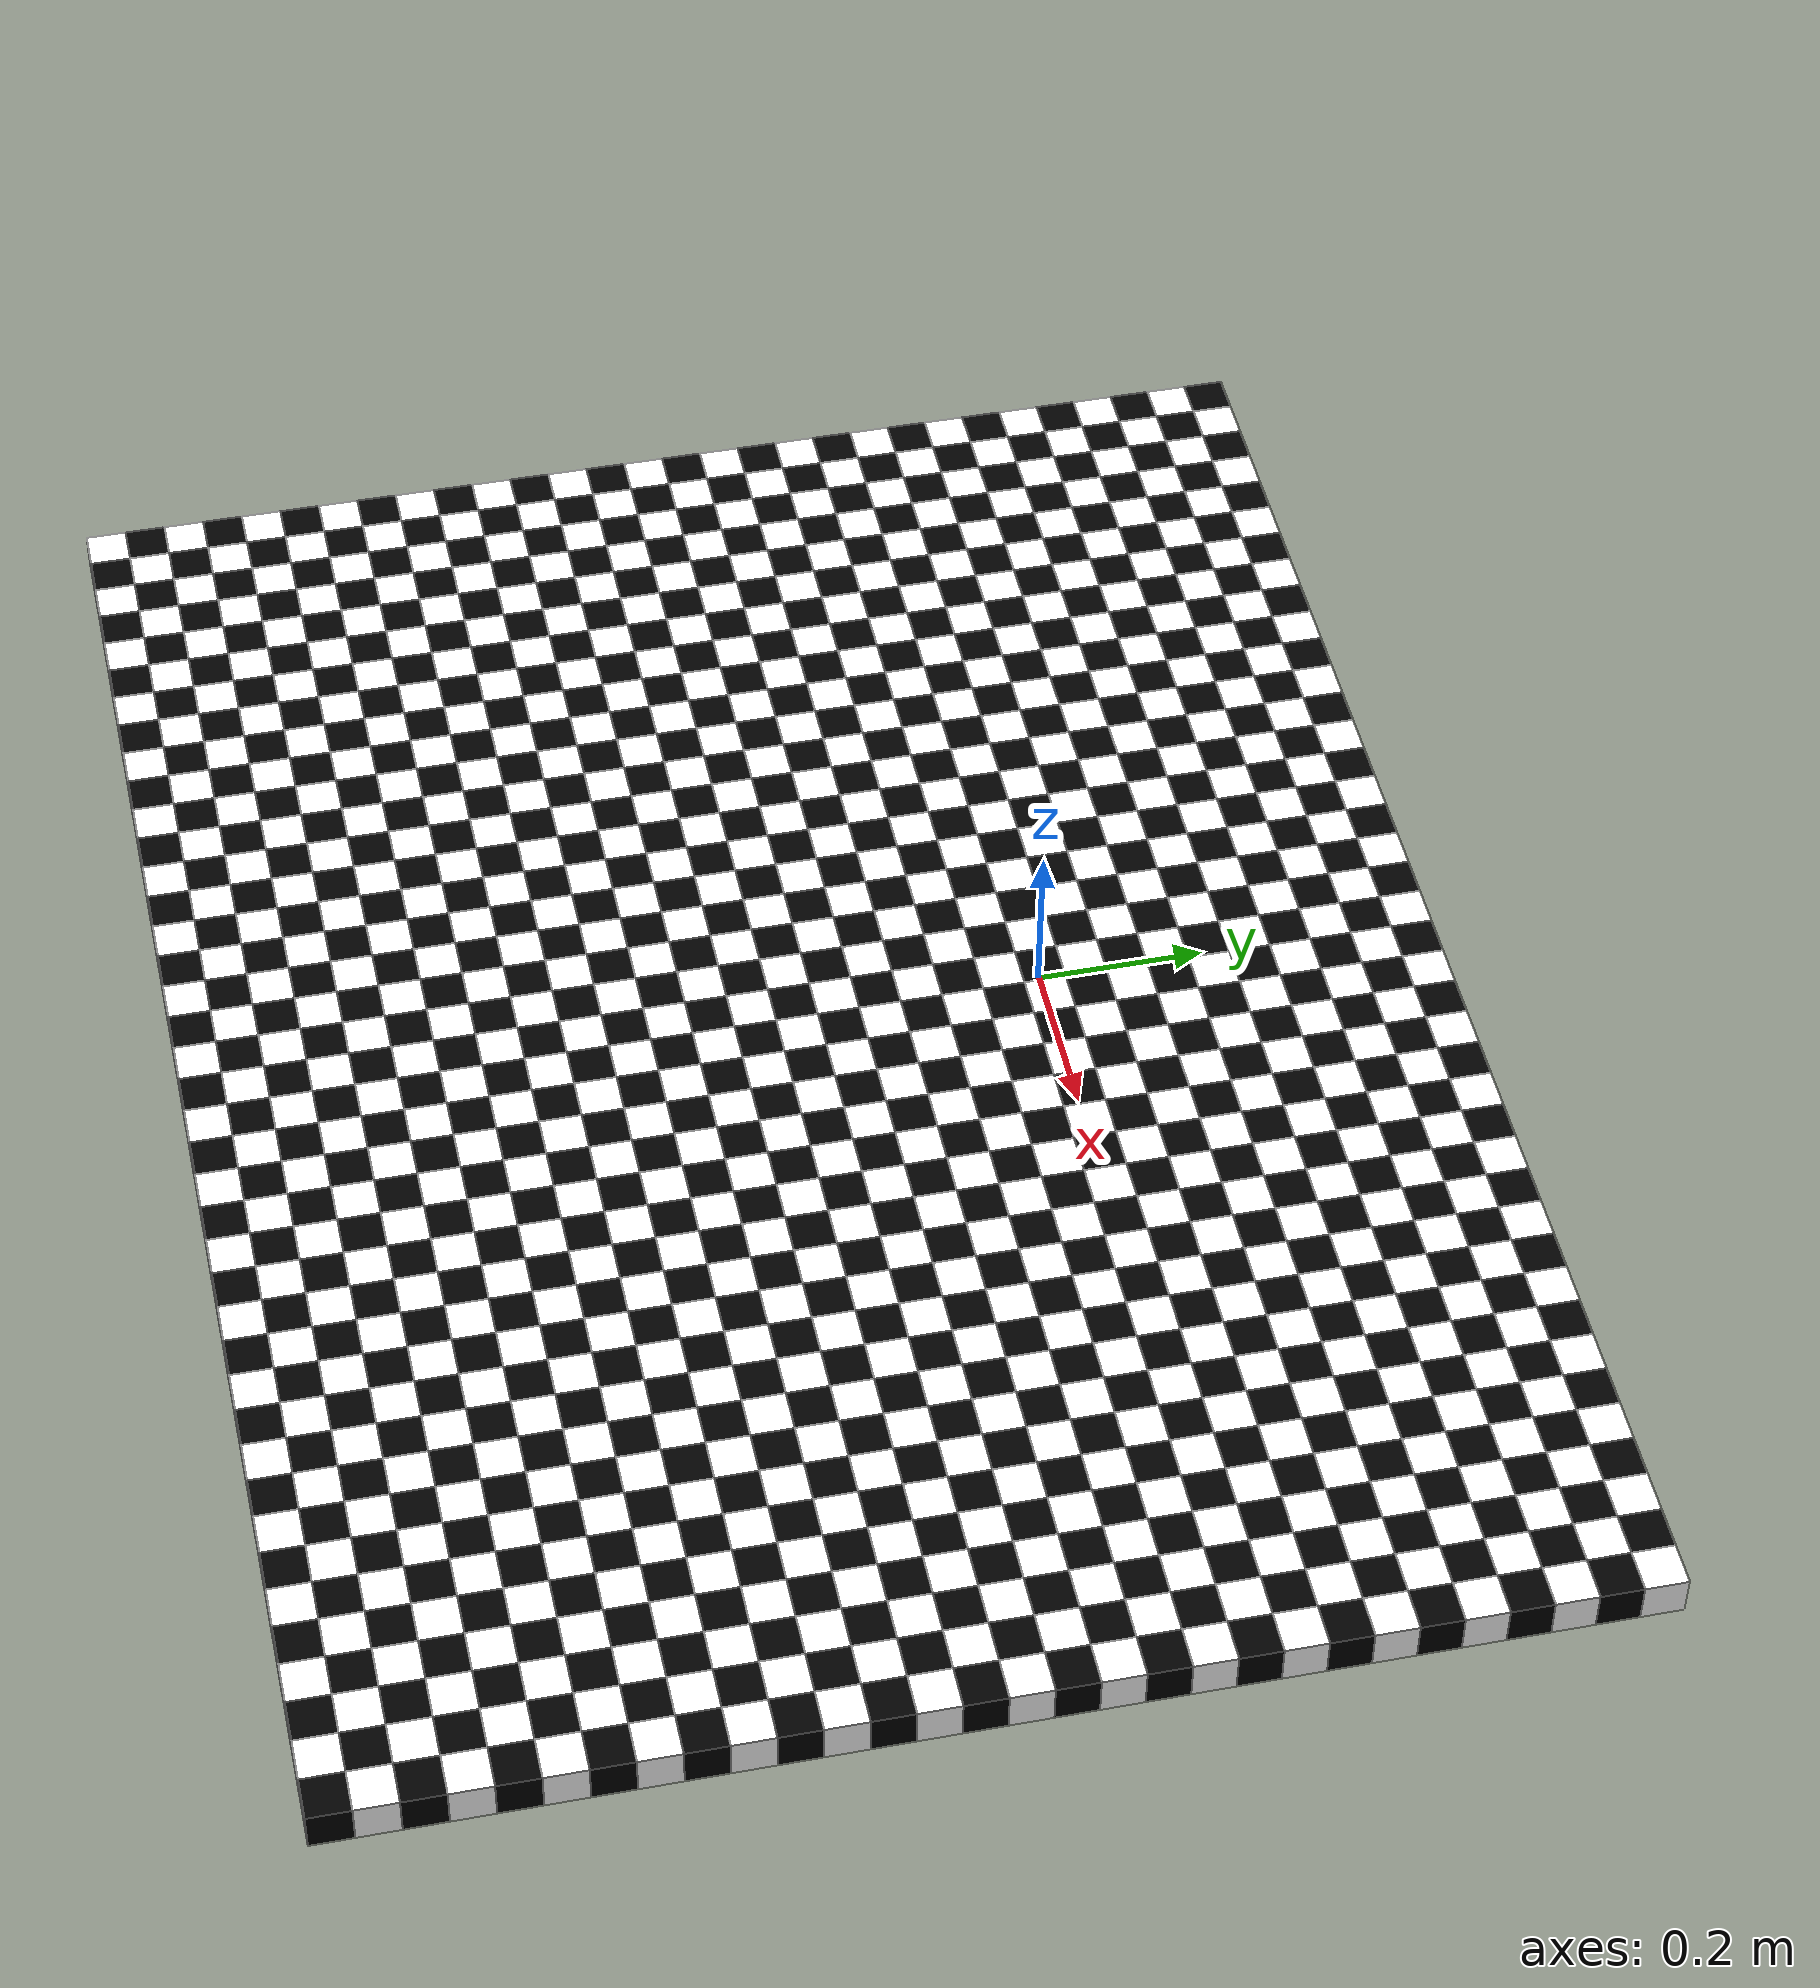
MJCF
<!-- This file was generated by build_floor.py -->
<!-- It is not recommended to edit this file -->
<mujoco>
    <default>
        <geom density="100" friction=".5" rgba="1 .6 .8 1" />
    </default>
    <worldbody>
        <geom type="box" size=".025 .025 .025" pos="-0.95 -1.0 0" rgba="1 1 1 1" />
<geom type="box" size=".025 .025 .025" pos="-0.8999999999999999 -1.0 0" rgba="0 0 0 1" />
<geom type="box" size=".025 .025 .025" pos="-0.85 -1.0 0" rgba="1 1 1 1" />
<geom type="box" size=".025 .025 .025" pos="-0.7999999999999999 -1.0 0" rgba="0 0 0 1" />
<geom type="box" size=".025 .025 .025" pos="-0.75 -1.0 0" rgba="1 1 1 1" />
<geom type="box" size=".025 .025 .025" pos="-0.7 -1.0 0" rgba="0 0 0 1" />
<geom type="box" size=".025 .025 .025" pos="-0.6499999999999999 -1.0 0" rgba="1 1 1 1" />
<geom type="box" size=".025 .025 .025" pos="-0.5999999999999999 -1.0 0" rgba="0 0 0 1" />
<geom type="box" size=".025 .025 .025" pos="-0.5499999999999999 -1.0 0" rgba="1 1 1 1" />
<geom type="box" size=".025 .025 .025" pos="-0.49999999999999994 -1.0 0" rgba="0 0 0 1" />
<geom type="box" size=".025 .025 .025" pos="-0.44999999999999996 -1.0 0" rgba="1 1 1 1" />
<geom type="box" size=".025 .025 .025" pos="-0.3999999999999999 -1.0 0" rgba="0 0 0 1" />
<geom type="box" size=".025 .025 .025" pos="-0.34999999999999987 -1.0 0" rgba="1 1 1 1" />
<geom type="box" size=".025 .025 .025" pos="-0.29999999999999993 -1.0 0" rgba="0 0 0 1" />
<geom type="box" size=".025 .025 .025" pos="-0.2499999999999999 -1.0 0" rgba="1 1 1 1" />
<geom type="box" size=".025 .025 .025" pos="-0.19999999999999996 -1.0 0" rgba="0 0 0 1" />
<geom type="box" size=".025 .025 .025" pos="-0.1499999999999999 -1.0 0" rgba="1 1 1 1" />
<geom type="box" size=".025 .025 .025" pos="-0.09999999999999987 -1.0 0" rgba="0 0 0 1" />
<geom type="box" size=".025 .025 .025" pos="-0.04999999999999993 -1.0 0" rgba="1 1 1 1" />
<geom type="box" size=".025 .025 .025" pos="1.1102230246251565e-16 -1.0 0" rgba="0 0 0 1" />
<geom type="box" size=".025 .025 .025" pos="0.050000000000000044 -1.0 0" rgba="1 1 1 1" />
<geom type="box" size=".025 .025 .025" pos="0.10000000000000009 -1.0 0" rgba="0 0 0 1" />
<geom type="box" size=".025 .025 .025" pos="0.15000000000000013 -1.0 0" rgba="1 1 1 1" />
<geom type="box" size=".025 .025 .025" pos="0.20000000000000018 -1.0 0" rgba="0 0 0 1" />
<geom type="box" size=".025 .025 .025" pos="0.2500000000000002 -1.0 0" rgba="1 1 1 1" />
<geom type="box" size=".025 .025 .025" pos="0.30000000000000004 -1.0 0" rgba="0 0 0 1" />
<geom type="box" size=".025 .025 .025" pos="0.3500000000000001 -1.0 0" rgba="1 1 1 1" />
<geom type="box" size=".025 .025 .025" pos="0.40000000000000013 -1.0 0" rgba="0 0 0 1" />
<geom type="box" size=".025 .025 .025" pos="0.4500000000000002 -1.0 0" rgba="1 1 1 1" />
<geom type="box" size=".025 .025 .025" pos="0.5000000000000002 -1.0 0" rgba="0 0 0 1" />
<geom type="box" size=".025 .025 .025" pos="0.55 -1.0 0" rgba="1 1 1 1" />
<geom type="box" size=".025 .025 .025" pos="0.6000000000000001 -1.0 0" rgba="0 0 0 1" />
<geom type="box" size=".025 .025 .025" pos="0.6500000000000001 -1.0 0" rgba="1 1 1 1" />
<geom type="box" size=".025 .025 .025" pos="0.7000000000000002 -1.0 0" rgba="0 0 0 1" />
<geom type="box" size=".025 .025 .025" pos="0.7500000000000002 -1.0 0" rgba="1 1 1 1" />
<geom type="box" size=".025 .025 .025" pos="0.8 -1.0 0" rgba="0 0 0 1" />
<geom type="box" size=".025 .025 .025" pos="0.8500000000000001 -1.0 0" rgba="1 1 1 1" />
<geom type="box" size=".025 .025 .025" pos="0.9000000000000001 -1.0 0" rgba="0 0 0 1" />
<geom type="box" size=".025 .025 .025" pos="0.9500000000000002 -1.0 0" rgba="1 1 1 1" />
<geom type="box" size=".025 .025 .025" pos="1.0000000000000002 -1.0 0" rgba="0 0 0 1" />
<geom type="box" size=".025 .025 .025" pos="-0.95 -0.95 0" rgba="0 0 0 1" />
<geom type="box" size=".025 .025 .025" pos="-0.8999999999999999 -0.95 0" rgba="1 1 1 1" />
<geom type="box" size=".025 .025 .025" pos="-0.85 -0.95 0" rgba="0 0 0 1" />
<geom type="box" size=".025 .025 .025" pos="-0.7999999999999999 -0.95 0" rgba="1 1 1 1" />
<geom type="box" size=".025 .025 .025" pos="-0.75 -0.95 0" rgba="0 0 0 1" />
<geom type="box" size=".025 .025 .025" pos="-0.7 -0.95 0" rgba="1 1 1 1" />
<geom type="box" size=".025 .025 .025" pos="-0.6499999999999999 -0.95 0" rgba="0 0 0 1" />
<geom type="box" size=".025 .025 .025" pos="-0.5999999999999999 -0.95 0" rgba="1 1 1 1" />
<geom type="box" size=".025 .025 .025" pos="-0.5499999999999999 -0.95 0" rgba="0 0 0 1" />
<geom type="box" size=".025 .025 .025" pos="-0.49999999999999994 -0.95 0" rgba="1 1 1 1" />
<geom type="box" size=".025 .025 .025" pos="-0.44999999999999996 -0.95 0" rgba="0 0 0 1" />
<geom type="box" size=".025 .025 .025" pos="-0.3999999999999999 -0.95 0" rgba="1 1 1 1" />
<geom type="box" size=".025 .025 .025" pos="-0.34999999999999987 -0.95 0" rgba="0 0 0 1" />
<geom type="box" size=".025 .025 .025" pos="-0.29999999999999993 -0.95 0" rgba="1 1 1 1" />
<geom type="box" size=".025 .025 .025" pos="-0.2499999999999999 -0.95 0" rgba="0 0 0 1" />
<geom type="box" size=".025 .025 .025" pos="-0.19999999999999996 -0.95 0" rgba="1 1 1 1" />
<geom type="box" size=".025 .025 .025" pos="-0.1499999999999999 -0.95 0" rgba="0 0 0 1" />
<geom type="box" size=".025 .025 .025" pos="-0.09999999999999987 -0.95 0" rgba="1 1 1 1" />
<geom type="box" size=".025 .025 .025" pos="-0.04999999999999993 -0.95 0" rgba="0 0 0 1" />
<geom type="box" size=".025 .025 .025" pos="1.1102230246251565e-16 -0.95 0" rgba="1 1 1 1" />
<geom type="box" size=".025 .025 .025" pos="0.050000000000000044 -0.95 0" rgba="0 0 0 1" />
<geom type="box" size=".025 .025 .025" pos="0.10000000000000009 -0.95 0" rgba="1 1 1 1" />
<geom type="box" size=".025 .025 .025" pos="0.15000000000000013 -0.95 0" rgba="0 0 0 1" />
<geom type="box" size=".025 .025 .025" pos="0.20000000000000018 -0.95 0" rgba="1 1 1 1" />
<geom type="box" size=".025 .025 .025" pos="0.2500000000000002 -0.95 0" rgba="0 0 0 1" />
<geom type="box" size=".025 .025 .025" pos="0.30000000000000004 -0.95 0" rgba="1 1 1 1" />
<geom type="box" size=".025 .025 .025" pos="0.3500000000000001 -0.95 0" rgba="0 0 0 1" />
<geom type="box" size=".025 .025 .025" pos="0.40000000000000013 -0.95 0" rgba="1 1 1 1" />
<geom type="box" size=".025 .025 .025" pos="0.4500000000000002 -0.95 0" rgba="0 0 0 1" />
<geom type="box" size=".025 .025 .025" pos="0.5000000000000002 -0.95 0" rgba="1 1 1 1" />
<geom type="box" size=".025 .025 .025" pos="0.55 -0.95 0" rgba="0 0 0 1" />
<geom type="box" size=".025 .025 .025" pos="0.6000000000000001 -0.95 0" rgba="1 1 1 1" />
<geom type="box" size=".025 .025 .025" pos="0.6500000000000001 -0.95 0" rgba="0 0 0 1" />
<geom type="box" size=".025 .025 .025" pos="0.7000000000000002 -0.95 0" rgba="1 1 1 1" />
<geom type="box" size=".025 .025 .025" pos="0.7500000000000002 -0.95 0" rgba="0 0 0 1" />
<geom type="box" size=".025 .025 .025" pos="0.8 -0.95 0" rgba="1 1 1 1" />
<geom type="box" size=".025 .025 .025" pos="0.8500000000000001 -0.95 0" rgba="0 0 0 1" />
<geom type="box" size=".025 .025 .025" pos="0.9000000000000001 -0.95 0" rgba="1 1 1 1" />
<geom type="box" size=".025 .025 .025" pos="0.9500000000000002 -0.95 0" rgba="0 0 0 1" />
<geom type="box" size=".025 .025 .025" pos="1.0000000000000002 -0.95 0" rgba="1 1 1 1" />
<geom type="box" size=".025 .025 .025" pos="-0.95 -0.9 0" rgba="1 1 1 1" />
<geom type="box" size=".025 .025 .025" pos="-0.8999999999999999 -0.9 0" rgba="0 0 0 1" />
<geom type="box" size=".025 .025 .025" pos="-0.85 -0.9 0" rgba="1 1 1 1" />
<geom type="box" size=".025 .025 .025" pos="-0.7999999999999999 -0.9 0" rgba="0 0 0 1" />
<geom type="box" size=".025 .025 .025" pos="-0.75 -0.9 0" rgba="1 1 1 1" />
<geom type="box" size=".025 .025 .025" pos="-0.7 -0.9 0" rgba="0 0 0 1" />
<geom type="box" size=".025 .025 .025" pos="-0.6499999999999999 -0.9 0" rgba="1 1 1 1" />
<geom type="box" size=".025 .025 .025" pos="-0.5999999999999999 -0.9 0" rgba="0 0 0 1" />
<geom type="box" size=".025 .025 .025" pos="-0.5499999999999999 -0.9 0" rgba="1 1 1 1" />
<geom type="box" size=".025 .025 .025" pos="-0.49999999999999994 -0.9 0" rgba="0 0 0 1" />
<geom type="box" size=".025 .025 .025" pos="-0.44999999999999996 -0.9 0" rgba="1 1 1 1" />
<geom type="box" size=".025 .025 .025" pos="-0.3999999999999999 -0.9 0" rgba="0 0 0 1" />
<geom type="box" size=".025 .025 .025" pos="-0.34999999999999987 -0.9 0" rgba="1 1 1 1" />
<geom type="box" size=".025 .025 .025" pos="-0.29999999999999993 -0.9 0" rgba="0 0 0 1" />
<geom type="box" size=".025 .025 .025" pos="-0.2499999999999999 -0.9 0" rgba="1 1 1 1" />
<geom type="box" size=".025 .025 .025" pos="-0.19999999999999996 -0.9 0" rgba="0 0 0 1" />
<geom type="box" size=".025 .025 .025" pos="-0.1499999999999999 -0.9 0" rgba="1 1 1 1" />
<geom type="box" size=".025 .025 .025" pos="-0.09999999999999987 -0.9 0" rgba="0 0 0 1" />
<geom type="box" size=".025 .025 .025" pos="-0.04999999999999993 -0.9 0" rgba="1 1 1 1" />
<geom type="box" size=".025 .025 .025" pos="1.1102230246251565e-16 -0.9 0" rgba="0 0 0 1" />
<geom type="box" size=".025 .025 .025" pos="0.050000000000000044 -0.9 0" rgba="1 1 1 1" />
<geom type="box" size=".025 .025 .025" pos="0.10000000000000009 -0.9 0" rgba="0 0 0 1" />
<geom type="box" size=".025 .025 .025" pos="0.15000000000000013 -0.9 0" rgba="1 1 1 1" />
<geom type="box" size=".025 .025 .025" pos="0.20000000000000018 -0.9 0" rgba="0 0 0 1" />
<geom type="box" size=".025 .025 .025" pos="0.2500000000000002 -0.9 0" rgba="1 1 1 1" />
<geom type="box" size=".025 .025 .025" pos="0.30000000000000004 -0.9 0" rgba="0 0 0 1" />
<geom type="box" size=".025 .025 .025" pos="0.3500000000000001 -0.9 0" rgba="1 1 1 1" />
<geom type="box" size=".025 .025 .025" pos="0.40000000000000013 -0.9 0" rgba="0 0 0 1" />
<geom type="box" size=".025 .025 .025" pos="0.4500000000000002 -0.9 0" rgba="1 1 1 1" />
<geom type="box" size=".025 .025 .025" pos="0.5000000000000002 -0.9 0" rgba="0 0 0 1" />
<geom type="box" size=".025 .025 .025" pos="0.55 -0.9 0" rgba="1 1 1 1" />
<geom type="box" size=".025 .025 .025" pos="0.6000000000000001 -0.9 0" rgba="0 0 0 1" />
<geom type="box" size=".025 .025 .025" pos="0.6500000000000001 -0.9 0" rgba="1 1 1 1" />
<geom type="box" size=".025 .025 .025" pos="0.7000000000000002 -0.9 0" rgba="0 0 0 1" />
<geom type="box" size=".025 .025 .025" pos="0.7500000000000002 -0.9 0" rgba="1 1 1 1" />
<geom type="box" size=".025 .025 .025" pos="0.8 -0.9 0" rgba="0 0 0 1" />
<geom type="box" size=".025 .025 .025" pos="0.8500000000000001 -0.9 0" rgba="1 1 1 1" />
<geom type="box" size=".025 .025 .025" pos="0.9000000000000001 -0.9 0" rgba="0 0 0 1" />
<geom type="box" size=".025 .025 .025" pos="0.9500000000000002 -0.9 0" rgba="1 1 1 1" />
<geom type="box" size=".025 .025 .025" pos="1.0000000000000002 -0.9 0" rgba="0 0 0 1" />
<geom type="box" size=".025 .025 .025" pos="-0.95 -0.85 0" rgba="0 0 0 1" />
<geom type="box" size=".025 .025 .025" pos="-0.8999999999999999 -0.85 0" rgba="1 1 1 1" />
<geom type="box" size=".025 .025 .025" pos="-0.85 -0.85 0" rgba="0 0 0 1" />
<geom type="box" size=".025 .025 .025" pos="-0.7999999999999999 -0.85 0" rgba="1 1 1 1" />
<geom type="box" size=".025 .025 .025" pos="-0.75 -0.85 0" rgba="0 0 0 1" />
<geom type="box" size=".025 .025 .025" pos="-0.7 -0.85 0" rgba="1 1 1 1" />
<geom type="box" size=".025 .025 .025" pos="-0.6499999999999999 -0.85 0" rgba="0 0 0 1" />
<geom type="box" size=".025 .025 .025" pos="-0.5999999999999999 -0.85 0" rgba="1 1 1 1" />
<geom type="box" size=".025 .025 .025" pos="-0.5499999999999999 -0.85 0" rgba="0 0 0 1" />
<geom type="box" size=".025 .025 .025" pos="-0.49999999999999994 -0.85 0" rgba="1 1 1 1" />
<geom type="box" size=".025 .025 .025" pos="-0.44999999999999996 -0.85 0" rgba="0 0 0 1" />
<geom type="box" size=".025 .025 .025" pos="-0.3999999999999999 -0.85 0" rgba="1 1 1 1" />
<geom type="box" size=".025 .025 .025" pos="-0.34999999999999987 -0.85 0" rgba="0 0 0 1" />
<geom type="box" size=".025 .025 .025" pos="-0.29999999999999993 -0.85 0" rgba="1 1 1 1" />
<geom type="box" size=".025 .025 .025" pos="-0.2499999999999999 -0.85 0" rgba="0 0 0 1" />
<geom type="box" size=".025 .025 .025" pos="-0.19999999999999996 -0.85 0" rgba="1 1 1 1" />
<geom type="box" size=".025 .025 .025" pos="-0.1499999999999999 -0.85 0" rgba="0 0 0 1" />
<geom type="box" size=".025 .025 .025" pos="-0.09999999999999987 -0.85 0" rgba="1 1 1 1" />
<geom type="box" size=".025 .025 .025" pos="-0.04999999999999993 -0.85 0" rgba="0 0 0 1" />
<geom type="box" size=".025 .025 .025" pos="1.1102230246251565e-16 -0.85 0" rgba="1 1 1 1" />
<geom type="box" size=".025 .025 .025" pos="0.050000000000000044 -0.85 0" rgba="0 0 0 1" />
<geom type="box" size=".025 .025 .025" pos="0.10000000000000009 -0.85 0" rgba="1 1 1 1" />
<geom type="box" size=".025 .025 .025" pos="0.15000000000000013 -0.85 0" rgba="0 0 0 1" />
<geom type="box" size=".025 .025 .025" pos="0.20000000000000018 -0.85 0" rgba="1 1 1 1" />
<geom type="box" size=".025 .025 .025" pos="0.2500000000000002 -0.85 0" rgba="0 0 0 1" />
<geom type="box" size=".025 .025 .025" pos="0.30000000000000004 -0.85 0" rgba="1 1 1 1" />
<geom type="box" size=".025 .025 .025" pos="0.3500000000000001 -0.85 0" rgba="0 0 0 1" />
<geom type="box" size=".025 .025 .025" pos="0.40000000000000013 -0.85 0" rgba="1 1 1 1" />
<geom type="box" size=".025 .025 .025" pos="0.4500000000000002 -0.85 0" rgba="0 0 0 1" />
<geom type="box" size=".025 .025 .025" pos="0.5000000000000002 -0.85 0" rgba="1 1 1 1" />
<geom type="box" size=".025 .025 .025" pos="0.55 -0.85 0" rgba="0 0 0 1" />
<geom type="box" size=".025 .025 .025" pos="0.6000000000000001 -0.85 0" rgba="1 1 1 1" />
<geom type="box" size=".025 .025 .025" pos="0.6500000000000001 -0.85 0" rgba="0 0 0 1" />
<geom type="box" size=".025 .025 .025" pos="0.7000000000000002 -0.85 0" rgba="1 1 1 1" />
<geom type="box" size=".025 .025 .025" pos="0.7500000000000002 -0.85 0" rgba="0 0 0 1" />
<geom type="box" size=".025 .025 .025" pos="0.8 -0.85 0" rgba="1 1 1 1" />
<geom type="box" size=".025 .025 .025" pos="0.8500000000000001 -0.85 0" rgba="0 0 0 1" />
<geom type="box" size=".025 .025 .025" pos="0.9000000000000001 -0.85 0" rgba="1 1 1 1" />
<geom type="box" size=".025 .025 .025" pos="0.9500000000000002 -0.85 0" rgba="0 0 0 1" />
<geom type="box" size=".025 .025 .025" pos="1.0000000000000002 -0.85 0" rgba="1 1 1 1" />
<geom type="box" size=".025 .025 .025" pos="-0.95 -0.8 0" rgba="1 1 1 1" />
<geom type="box" size=".025 .025 .025" pos="-0.8999999999999999 -0.8 0" rgba="0 0 0 1" />
<geom type="box" size=".025 .025 .025" pos="-0.85 -0.8 0" rgba="1 1 1 1" />
<geom type="box" size=".025 .025 .025" pos="-0.7999999999999999 -0.8 0" rgba="0 0 0 1" />
<geom type="box" size=".025 .025 .025" pos="-0.75 -0.8 0" rgba="1 1 1 1" />
<geom type="box" size=".025 .025 .025" pos="-0.7 -0.8 0" rgba="0 0 0 1" />
<geom type="box" size=".025 .025 .025" pos="-0.6499999999999999 -0.8 0" rgba="1 1 1 1" />
<geom type="box" size=".025 .025 .025" pos="-0.5999999999999999 -0.8 0" rgba="0 0 0 1" />
<geom type="box" size=".025 .025 .025" pos="-0.5499999999999999 -0.8 0" rgba="1 1 1 1" />
<geom type="box" size=".025 .025 .025" pos="-0.49999999999999994 -0.8 0" rgba="0 0 0 1" />
<geom type="box" size=".025 .025 .025" pos="-0.44999999999999996 -0.8 0" rgba="1 1 1 1" />
<geom type="box" size=".025 .025 .025" pos="-0.3999999999999999 -0.8 0" rgba="0 0 0 1" />
<geom type="box" size=".025 .025 .025" pos="-0.34999999999999987 -0.8 0" rgba="1 1 1 1" />
<geom type="box" size=".025 .025 .025" pos="-0.29999999999999993 -0.8 0" rgba="0 0 0 1" />
<geom type="box" size=".025 .025 .025" pos="-0.2499999999999999 -0.8 0" rgba="1 1 1 1" />
<geom type="box" size=".025 .025 .025" pos="-0.19999999999999996 -0.8 0" rgba="0 0 0 1" />
<geom type="box" size=".025 .025 .025" pos="-0.1499999999999999 -0.8 0" rgba="1 1 1 1" />
<geom type="box" size=".025 .025 .025" pos="-0.09999999999999987 -0.8 0" rgba="0 0 0 1" />
<geom type="box" size=".025 .025 .025" pos="-0.04999999999999993 -0.8 0" rgba="1 1 1 1" />
<geom type="box" size=".025 .025 .025" pos="1.1102230246251565e-16 -0.8 0" rgba="0 0 0 1" />
<geom type="box" size=".025 .025 .025" pos="0.050000000000000044 -0.8 0" rgba="1 1 1 1" />
<geom type="box" size=".025 .025 .025" pos="0.10000000000000009 -0.8 0" rgba="0 0 0 1" />
<geom type="box" size=".025 .025 .025" pos="0.15000000000000013 -0.8 0" rgba="1 1 1 1" />
<geom type="box" size=".025 .025 .025" pos="0.20000000000000018 -0.8 0" rgba="0 0 0 1" />
<geom type="box" size=".025 .025 .025" pos="0.2500000000000002 -0.8 0" rgba="1 1 1 1" />
<geom type="box" size=".025 .025 .025" pos="0.30000000000000004 -0.8 0" rgba="0 0 0 1" />
<geom type="box" size=".025 .025 .025" pos="0.3500000000000001 -0.8 0" rgba="1 1 1 1" />
<geom type="box" size=".025 .025 .025" pos="0.40000000000000013 -0.8 0" rgba="0 0 0 1" />
<geom type="box" size=".025 .025 .025" pos="0.4500000000000002 -0.8 0" rgba="1 1 1 1" />
<geom type="box" size=".025 .025 .025" pos="0.5000000000000002 -0.8 0" rgba="0 0 0 1" />
<geom type="box" size=".025 .025 .025" pos="0.55 -0.8 0" rgba="1 1 1 1" />
<geom type="box" size=".025 .025 .025" pos="0.6000000000000001 -0.8 0" rgba="0 0 0 1" />
<geom type="box" size=".025 .025 .025" pos="0.6500000000000001 -0.8 0" rgba="1 1 1 1" />
<geom type="box" size=".025 .025 .025" pos="0.7000000000000002 -0.8 0" rgba="0 0 0 1" />
<geom type="box" size=".025 .025 .025" pos="0.7500000000000002 -0.8 0" rgba="1 1 1 1" />
<geom type="box" size=".025 .025 .025" pos="0.8 -0.8 0" rgba="0 0 0 1" />
<geom type="box" size=".025 .025 .025" pos="0.8500000000000001 -0.8 0" rgba="1 1 1 1" />
<geom type="box" size=".025 .025 .025" pos="0.9000000000000001 -0.8 0" rgba="0 0 0 1" />
<geom type="box" size=".025 .025 .025" pos="0.9500000000000002 -0.8 0" rgba="1 1 1 1" />
<geom type="box" size=".025 .025 .025" pos="1.0000000000000002 -0.8 0" rgba="0 0 0 1" />
<geom type="box" size=".025 .025 .025" pos="-0.95 -0.75 0" rgba="0 0 0 1" />
<geom type="box" size=".025 .025 .025" pos="-0.8999999999999999 -0.75 0" rgba="1 1 1 1" />
<geom type="box" size=".025 .025 .025" pos="-0.85 -0.75 0" rgba="0 0 0 1" />
<geom type="box" size=".025 .025 .025" pos="-0.7999999999999999 -0.75 0" rgba="1 1 1 1" />
<geom type="box" size=".025 .025 .025" pos="-0.75 -0.75 0" rgba="0 0 0 1" />
<geom type="box" size=".025 .025 .025" pos="-0.7 -0.75 0" rgba="1 1 1 1" />
<geom type="box" size=".025 .025 .025" pos="-0.6499999999999999 -0.75 0" rgba="0 0 0 1" />
<geom type="box" size=".025 .025 .025" pos="-0.5999999999999999 -0.75 0" rgba="1 1 1 1" />
<geom type="box" size=".025 .025 .025" pos="-0.5499999999999999 -0.75 0" rgba="0 0 0 1" />
<geom type="box" size=".025 .025 .025" pos="-0.49999999999999994 -0.75 0" rgba="1 1 1 1" />
<geom type="box" size=".025 .025 .025" pos="-0.44999999999999996 -0.75 0" rgba="0 0 0 1" />
<geom type="box" size=".025 .025 .025" pos="-0.3999999999999999 -0.75 0" rgba="1 1 1 1" />
<geom type="box" size=".025 .025 .025" pos="-0.34999999999999987 -0.75 0" rgba="0 0 0 1" />
<geom type="box" size=".025 .025 .025" pos="-0.29999999999999993 -0.75 0" rgba="1 1 1 1" />
<geom type="box" size=".025 .025 .025" pos="-0.2499999999999999 -0.75 0" rgba="0 0 0 1" />
<geom type="box" size=".025 .025 .025" pos="-0.19999999999999996 -0.75 0" rgba="1 1 1 1" />
<geom type="box" size=".025 .025 .025" pos="-0.1499999999999999 -0.75 0" rgba="0 0 0 1" />
<geom type="box" size=".025 .025 .025" pos="-0.09999999999999987 -0.75 0" rgba="1 1 1 1" />
<geom type="box" size=".025 .025 .025" pos="-0.04999999999999993 -0.75 0" rgba="0 0 0 1" />
<geom type="box" size=".025 .025 .025" pos="1.1102230246251565e-16 -0.75 0" rgba="1 1 1 1" />
<geom type="box" size=".025 .025 .025" pos="0.050000000000000044 -0.75 0" rgba="0 0 0 1" />
<geom type="box" size=".025 .025 .025" pos="0.10000000000000009 -0.75 0" rgba="1 1 1 1" />
<geom type="box" size=".025 .025 .025" pos="0.15000000000000013 -0.75 0" rgba="0 0 0 1" />
<geom type="box" size=".025 .025 .025" pos="0.20000000000000018 -0.75 0" rgba="1 1 1 1" />
<geom type="box" size=".025 .025 .025" pos="0.2500000000000002 -0.75 0" rgba="0 0 0 1" />
<geom type="box" size=".025 .025 .025" pos="0.30000000000000004 -0.75 0" rgba="1 1 1 1" />
<geom type="box" size=".025 .025 .025" pos="0.3500000000000001 -0.75 0" rgba="0 0 0 1" />
<geom type="box" size=".025 .025 .025" pos="0.40000000000000013 -0.75 0" rgba="1 1 1 1" />
<geom type="box" size=".025 .025 .025" pos="0.4500000000000002 -0.75 0" rgba="0 0 0 1" />
<geom type="box" size=".025 .025 .025" pos="0.5000000000000002 -0.75 0" rgba="1 1 1 1" />
<geom type="box" size=".025 .025 .025" pos="0.55 -0.75 0" rgba="0 0 0 1" />
<geom type="box" size=".025 .025 .025" pos="0.6000000000000001 -0.75 0" rgba="1 1 1 1" />
<geom type="box" size=".025 .025 .025" pos="0.6500000000000001 -0.75 0" rgba="0 0 0 1" />
<geom type="box" size=".025 .025 .025" pos="0.7000000000000002 -0.75 0" rgba="1 1 1 1" />
<geom type="box" size=".025 .025 .025" pos="0.7500000000000002 -0.75 0" rgba="0 0 0 1" />
<geom type="box" size=".025 .025 .025" pos="0.8 -0.75 0" rgba="1 1 1 1" />
<geom type="box" size=".025 .025 .025" pos="0.8500000000000001 -0.75 0" rgba="0 0 0 1" />
<geom type="box" size=".025 .025 .025" pos="0.9000000000000001 -0.75 0" rgba="1 1 1 1" />
<geom type="box" size=".025 .025 .025" pos="0.9500000000000002 -0.75 0" rgba="0 0 0 1" />
<geom type="box" size=".025 .025 .025" pos="1.0000000000000002 -0.75 0" rgba="1 1 1 1" />
<geom type="box" size=".025 .025 .025" pos="-0.95 -0.7 0" rgba="1 1 1 1" />
<geom type="box" size=".025 .025 .025" pos="-0.8999999999999999 -0.7 0" rgba="0 0 0 1" />
<geom type="box" size=".025 .025 .025" pos="-0.85 -0.7 0" rgba="1 1 1 1" />
<geom type="box" size=".025 .025 .025" pos="-0.7999999999999999 -0.7 0" rgba="0 0 0 1" />
<geom type="box" size=".025 .025 .025" pos="-0.75 -0.7 0" rgba="1 1 1 1" />
<geom type="box" size=".025 .025 .025" pos="-0.7 -0.7 0" rgba="0 0 0 1" />
<geom type="box" size=".025 .025 .025" pos="-0.6499999999999999 -0.7 0" rgba="1 1 1 1" />
<geom type="box" size=".025 .025 .025" pos="-0.5999999999999999 -0.7 0" rgba="0 0 0 1" />
<geom type="box" size=".025 .025 .025" pos="-0.5499999999999999 -0.7 0" rgba="1 1 1 1" />
<geom type="box" size=".025 .025 .025" pos="-0.49999999999999994 -0.7 0" rgba="0 0 0 1" />
<geom type="box" size=".025 .025 .025" pos="-0.44999999999999996 -0.7 0" rgba="1 1 1 1" />
<geom type="box" size=".025 .025 .025" pos="-0.3999999999999999 -0.7 0" rgba="0 0 0 1" />
<geom type="box" size=".025 .025 .025" pos="-0.34999999999999987 -0.7 0" rgba="1 1 1 1" />
<geom type="box" size=".025 .025 .025" pos="-0.29999999999999993 -0.7 0" rgba="0 0 0 1" />
<geom type="box" size=".025 .025 .025" pos="-0.2499999999999999 -0.7 0" rgba="1 1 1 1" />
<geom type="box" size=".025 .025 .025" pos="-0.19999999999999996 -0.7 0" rgba="0 0 0 1" />
<geom type="box" size=".025 .025 .025" pos="-0.1499999999999999 -0.7 0" rgba="1 1 1 1" />
<geom type="box" size=".025 .025 .025" pos="-0.09999999999999987 -0.7 0" rgba="0 0 0 1" />
<geom type="box" size=".025 .025 .025" pos="-0.04999999999999993 -0.7 0" rgba="1 1 1 1" />
<geom type="box" size=".025 .025 .025" pos="1.1102230246251565e-16 -0.7 0" rgba="0 0 0 1" />
<geom type="box" size=".025 .025 .025" pos="0.050000000000000044 -0.7 0" rgba="1 1 1 1" />
<geom type="box" size=".025 .025 .025" pos="0.10000000000000009 -0.7 0" rgba="0 0 0 1" />
<geom type="box" size=".025 .025 .025" pos="0.15000000000000013 -0.7 0" rgba="1 1 1 1" />
<geom type="box" size=".025 .025 .025" pos="0.20000000000000018 -0.7 0" rgba="0 0 0 1" />
<geom type="box" size=".025 .025 .025" pos="0.2500000000000002 -0.7 0" rgba="1 1 1 1" />
<geom type="box" size=".025 .025 .025" pos="0.30000000000000004 -0.7 0" rgba="0 0 0 1" />
<geom type="box" size=".025 .025 .025" pos="0.3500000000000001 -0.7 0" rgba="1 1 1 1" />
<geom type="box" size=".025 .025 .025" pos="0.40000000000000013 -0.7 0" rgba="0 0 0 1" />
<geom type="box" size=".025 .025 .025" pos="0.4500000000000002 -0.7 0" rgba="1 1 1 1" />
<geom type="box" size=".025 .025 .025" pos="0.5000000000000002 -0.7 0" rgba="0 0 0 1" />
<geom type="box" size=".025 .025 .025" pos="0.55 -0.7 0" rgba="1 1 1 1" />
<geom type="box" size=".025 .025 .025" pos="0.6000000000000001 -0.7 0" rgba="0 0 0 1" />
<geom type="box" size=".025 .025 .025" pos="0.6500000000000001 -0.7 0" rgba="1 1 1 1" />
<geom type="box" size=".025 .025 .025" pos="0.7000000000000002 -0.7 0" rgba="0 0 0 1" />
<geom type="box" size=".025 .025 .025" pos="0.7500000000000002 -0.7 0" rgba="1 1 1 1" />
<geom type="box" size=".025 .025 .025" pos="0.8 -0.7 0" rgba="0 0 0 1" />
<geom type="box" size=".025 .025 .025" pos="0.8500000000000001 -0.7 0" rgba="1 1 1 1" />
<geom type="box" size=".025 .025 .025" pos="0.9000000000000001 -0.7 0" rgba="0 0 0 1" />
<geom type="box" size=".025 .025 .025" pos="0.9500000000000002 -0.7 0" rgba="1 1 1 1" />
<geom type="box" size=".025 .025 .025" pos="1.0000000000000002 -0.7 0" rgba="0 0 0 1" />
<geom type="box" size=".025 .025 .025" pos="-0.95 -0.6499999999999999 0" rgba="0 0 0 1" />
<geom type="box" size=".025 .025 .025" pos="-0.8999999999999999 -0.6499999999999999 0" rgba="1 1 1 1" />
<geom type="box" size=".025 .025 .025" pos="-0.85 -0.6499999999999999 0" rgba="0 0 0 1" />
<geom type="box" size=".025 .025 .025" pos="-0.7999999999999999 -0.6499999999999999 0" rgba="1 1 1 1" />
<geom type="box" size=".025 .025 .025" pos="-0.75 -0.6499999999999999 0" rgba="0 0 0 1" />
<geom type="box" size=".025 .025 .025" pos="-0.7 -0.6499999999999999 0" rgba="1 1 1 1" />
<geom type="box" size=".025 .025 .025" pos="-0.6499999999999999 -0.6499999999999999 0" rgba="0 0 0 1" />
<geom type="box" size=".025 .025 .025" pos="-0.5999999999999999 -0.6499999999999999 0" rgba="1 1 1 1" />
<geom type="box" size=".025 .025 .025" pos="-0.5499999999999999 -0.6499999999999999 0" rgba="0 0 0 1" />
<geom type="box" size=".025 .025 .025" pos="-0.49999999999999994 -0.6499999999999999 0" rgba="1 1 1 1" />
<geom type="box" size=".025 .025 .025" pos="-0.44999999999999996 -0.6499999999999999 0" rgba="0 0 0 1" />
<geom type="box" size=".025 .025 .025" pos="-0.3999999999999999 -0.6499999999999999 0" rgba="1 1 1 1" />
<geom type="box" size=".025 .025 .025" pos="-0.34999999999999987 -0.6499999999999999 0" rgba="0 0 0 1" />
<geom type="box" size=".025 .025 .025" pos="-0.29999999999999993 -0.6499999999999999 0" rgba="1 1 1 1" />
<geom type="box" size=".025 .025 .025" pos="-0.2499999999999999 -0.6499999999999999 0" rgba="0 0 0 1" />
<geom type="box" size=".025 .025 .025" pos="-0.19999999999999996 -0.6499999999999999 0" rgba="1 1 1 1" />
<geom type="box" size=".025 .025 .025" pos="-0.1499999999999999 -0.6499999999999999 0" rgba="0 0 0 1" />
<geom type="box" size=".025 .025 .025" pos="-0.09999999999999987 -0.6499999999999999 0" rgba="1 1 1 1" />
<geom type="box" size=".025 .025 .025" pos="-0.04999999999999993 -0.6499999999999999 0" rgba="0 0 0 1" />
<geom type="box" size=".025 .025 .025" pos="1.1102230246251565e-16 -0.6499999999999999 0" rgba="1 1 1 1" />
<geom type="box" size=".025 .025 .025" pos="0.050000000000000044 -0.6499999999999999 0" rgba="0 0 0 1" />
<geom type="box" size=".025 .025 .025" pos="0.10000000000000009 -0.6499999999999999 0" rgba="1 1 1 1" />
<geom type="box" size=".025 .025 .025" pos="0.15000000000000013 -0.6499999999999999 0" rgba="0 0 0 1" />
<geom type="box" size=".025 .025 .025" pos="0.20000000000000018 -0.6499999999999999 0" rgba="1 1 1 1" />
<geom type="box" size=".025 .025 .025" pos="0.2500000000000002 -0.6499999999999999 0" rgba="0 0 0 1" />
<geom type="box" size=".025 .025 .025" pos="0.30000000000000004 -0.6499999999999999 0" rgba="1 1 1 1" />
<geom type="box" size=".025 .025 .025" pos="0.3500000000000001 -0.6499999999999999 0" rgba="0 0 0 1" />
<geom type="box" size=".025 .025 .025" pos="0.40000000000000013 -0.6499999999999999 0" rgba="1 1 1 1" />
<geom type="box" size=".025 .025 .025" pos="0.4500000000000002 -0.6499999999999999 0" rgba="0 0 0 1" />
<geom type="box" size=".025 .025 .025" pos="0.5000000000000002 -0.6499999999999999 0" rgba="1 1 1 1" />
<geom type="box" size=".025 .025 .025" pos="0.55 -0.6499999999999999 0" rgba="0 0 0 1" />
<geom type="box" size=".025 .025 .025" pos="0.6000000000000001 -0.6499999999999999 0" rgba="1 1 1 1" />
<geom type="box" size=".025 .025 .025" pos="0.6500000000000001 -0.6499999999999999 0" rgba="0 0 0 1" />
<geom type="box" size=".025 .025 .025" pos="0.7000000000000002 -0.6499999999999999 0" rgba="1 1 1 1" />
<geom type="box" size=".025 .025 .025" pos="0.7500000000000002 -0.6499999999999999 0" rgba="0 0 0 1" />
<geom type="box" size=".025 .025 .025" pos="0.8 -0.6499999999999999 0" rgba="1 1 1 1" />
<geom type="box" size=".025 .025 .025" pos="0.8500000000000001 -0.6499999999999999 0" rgba="0 0 0 1" />
<geom type="box" size=".025 .025 .025" pos="0.9000000000000001 -0.6499999999999999 0" rgba="1 1 1 1" />
<geom type="box" size=".025 .025 .025" pos="0.9500000000000002 -0.6499999999999999 0" rgba="0 0 0 1" />
<geom type="box" size=".025 .025 .025" pos="1.0000000000000002 -0.6499999999999999 0" rgba="1 1 1 1" />
<geom type="box" size=".025 .025 .025" pos="-0.95 -0.6 0" rgba="1 1 1 1" />
<geom type="box" size=".025 .025 .025" pos="-0.8999999999999999 -0.6 0" rgba="0 0 0 1" />
<geom type="box" size=".025 .025 .025" pos="-0.85 -0.6 0" rgba="1 1 1 1" />
<geom type="box" size=".025 .025 .025" pos="-0.7999999999999999 -0.6 0" rgba="0 0 0 1" />
<geom type="box" size=".025 .025 .025" pos="-0.75 -0.6 0" rgba="1 1 1 1" />
<geom type="box" size=".025 .025 .025" pos="-0.7 -0.6 0" rgba="0 0 0 1" />
<geom type="box" size=".025 .025 .025" pos="-0.6499999999999999 -0.6 0" rgba="1 1 1 1" />
<geom type="box" size=".025 .025 .025" pos="-0.5999999999999999 -0.6 0" rgba="0 0 0 1" />
<geom type="box" size=".025 .025 .025" pos="-0.5499999999999999 -0.6 0" rgba="1 1 1 1" />
<geom type="box" size=".025 .025 .025" pos="-0.49999999999999994 -0.6 0" rgba="0 0 0 1" />
<geom type="box" size=".025 .025 .025" pos="-0.44999999999999996 -0.6 0" rgba="1 1 1 1" />
<geom type="box" size=".025 .025 .025" pos="-0.3999999999999999 -0.6 0" rgba="0 0 0 1" />
<geom type="box" size=".025 .025 .025" pos="-0.34999999999999987 -0.6 0" rgba="1 1 1 1" />
<geom type="box" size=".025 .025 .025" pos="-0.29999999999999993 -0.6 0" rgba="0 0 0 1" />
<geom type="box" size=".025 .025 .025" pos="-0.2499999999999999 -0.6 0" rgba="1 1 1 1" />
<geom type="box" size=".025 .025 .025" pos="-0.19999999999999996 -0.6 0" rgba="0 0 0 1" />
<geom type="box" size=".025 .025 .025" pos="-0.1499999999999999 -0.6 0" rgba="1 1 1 1" />
<geom type="box" size=".025 .025 .025" pos="-0.09999999999999987 -0.6 0" rgba="0 0 0 1" />
<geom type="box" size=".025 .025 .025" pos="-0.04999999999999993 -0.6 0" rgba="1 1 1 1" />
<geom type="box" size=".025 .025 .025" pos="1.1102230246251565e-16 -0.6 0" rgba="0 0 0 1" />
<geom type="box" size=".025 .025 .025" pos="0.050000000000000044 -0.6 0" rgba="1 1 1 1" />
<geom type="box" size=".025 .025 .025" pos="0.10000000000000009 -0.6 0" rgba="0 0 0 1" />
<geom type="box" size=".025 .025 .025" pos="0.15000000000000013 -0.6 0" rgba="1 1 1 1" />
<geom type="box" size=".025 .025 .025" pos="0.20000000000000018 -0.6 0" rgba="0 0 0 1" />
<geom type="box" size=".025 .025 .025" pos="0.2500000000000002 -0.6 0" rgba="1 1 1 1" />
<geom type="box" size=".025 .025 .025" pos="0.30000000000000004 -0.6 0" rgba="0 0 0 1" />
<geom type="box" size=".025 .025 .025" pos="0.3500000000000001 -0.6 0" rgba="1 1 1 1" />
<geom type="box" size=".025 .025 .025" pos="0.40000000000000013 -0.6 0" rgba="0 0 0 1" />
<geom type="box" size=".025 .025 .025" pos="0.4500000000000002 -0.6 0" rgba="1 1 1 1" />
<geom type="box" size=".025 .025 .025" pos="0.5000000000000002 -0.6 0" rgba="0 0 0 1" />
<geom type="box" size=".025 .025 .025" pos="0.55 -0.6 0" rgba="1 1 1 1" />
<geom type="box" size=".025 .025 .025" pos="0.6000000000000001 -0.6 0" rgba="0 0 0 1" />
<geom type="box" size=".025 .025 .025" pos="0.6500000000000001 -0.6 0" rgba="1 1 1 1" />
<geom type="box" size=".025 .025 .025" pos="0.7000000000000002 -0.6 0" rgba="0 0 0 1" />
<geom type="box" size=".025 .025 .025" pos="0.7500000000000002 -0.6 0" rgba="1 1 1 1" />
<geom type="box" size=".025 .025 .025" pos="0.8 -0.6 0" rgba="0 0 0 1" />
<geom type="box" size=".025 .025 .025" pos="0.8500000000000001 -0.6 0" rgba="1 1 1 1" />
<geom type="box" size=".025 .025 .025" pos="0.9000000000000001 -0.6 0" rgba="0 0 0 1" />
<geom type="box" size=".025 .025 .025" pos="0.9500000000000002 -0.6 0" rgba="1 1 1 1" />
<geom type="box" size=".025 .025 .025" pos="1.0000000000000002 -0.6 0" rgba="0 0 0 1" />
<geom type="box" size=".025 .025 .025" pos="-0.95 -0.55 0" rgba="0 0 0 1" />
<geom type="box" size=".025 .025 .025" pos="-0.8999999999999999 -0.55 0" rgba="1 1 1 1" />
<geom type="box" size=".025 .025 .025" pos="-0.85 -0.55 0" rgba="0 0 0 1" />
<geom type="box" size=".025 .025 .025" pos="-0.7999999999999999 -0.55 0" rgba="1 1 1 1" />
<geom type="box" size=".025 .025 .025" pos="-0.75 -0.55 0" rgba="0 0 0 1" />
<geom type="box" size=".025 .025 .025" pos="-0.7 -0.55 0" rgba="1 1 1 1" />
<geom type="box" size=".025 .025 .025" pos="-0.6499999999999999 -0.55 0" rgba="0 0 0 1" />
<geom type="box" size=".025 .025 .025" pos="-0.5999999999999999 -0.55 0" rgba="1 1 1 1" />
<geom type="box" size=".025 .025 .025" pos="-0.5499999999999999 -0.55 0" rgba="0 0 0 1" />
<geom type="box" size=".025 .025 .025" pos="-0.49999999999999994 -0.55 0" rgba="1 1 1 1" />
<geom type="box" size=".025 .025 .025" pos="-0.44999999999999996 -0.55 0" rgba="0 0 0 1" />
<geom type="box" size=".025 .025 .025" pos="-0.3999999999999999 -0.55 0" rgba="1 1 1 1" />
<geom type="box" size=".025 .025 .025" pos="-0.34999999999999987 -0.55 0" rgba="0 0 0 1" />
<geom type="box" size=".025 .025 .025" pos="-0.29999999999999993 -0.55 0" rgba="1 1 1 1" />
<geom type="box" size=".025 .025 .025" pos="-0.2499999999999999 -0.55 0" rgba="0 0 0 1" />
<geom type="box" size=".025 .025 .025" pos="-0.19999999999999996 -0.55 0" rgba="1 1 1 1" />
<geom type="box" size=".025 .025 .025" pos="-0.1499999999999999 -0.55 0" rgba="0 0 0 1" />
<geom type="box" size=".025 .025 .025" pos="-0.09999999999999987 -0.55 0" rgba="1 1 1 1" />
<geom type="box" size=".025 .025 .025" pos="-0.04999999999999993 -0.55 0" rgba="0 0 0 1" />
<geom type="box" size=".025 .025 .025" pos="1.1102230246251565e-16 -0.55 0" rgba="1 1 1 1" />
<geom type="box" size=".025 .025 .025" pos="0.050000000000000044 -0.55 0" rgba="0 0 0 1" />
<geom type="box" size=".025 .025 .025" pos="0.10000000000000009 -0.55 0" rgba="1 1 1 1" />
<geom type="box" size=".025 .025 .025" pos="0.15000000000000013 -0.55 0" rgba="0 0 0 1" />
<geom type="box" size=".025 .025 .025" pos="0.20000000000000018 -0.55 0" rgba="1 1 1 1" />
<geom type="box" size=".025 .025 .025" pos="0.2500000000000002 -0.55 0" rgba="0 0 0 1" />
<geom type="box" size=".025 .025 .025" pos="0.30000000000000004 -0.55 0" rgba="1 1 1 1" />
<geom type="box" size=".025 .025 .025" pos="0.3500000000000001 -0.55 0" rgba="0 0 0 1" />
<geom type="box" size=".025 .025 .025" pos="0.40000000000000013 -0.55 0" rgba="1 1 1 1" />
<geom type="box" size=".025 .025 .025" pos="0.4500000000000002 -0.55 0" rgba="0 0 0 1" />
<geom type="box" size=".025 .025 .025" pos="0.5000000000000002 -0.55 0" rgba="1 1 1 1" />
<geom type="box" size=".025 .025 .025" pos="0.55 -0.55 0" rgba="0 0 0 1" />
<geom type="box" size=".025 .025 .025" pos="0.6000000000000001 -0.55 0" rgba="1 1 1 1" />
<geom type="box" size=".025 .025 .025" pos="0.6500000000000001 -0.55 0" rgba="0 0 0 1" />
<geom type="box" size=".025 .025 .025" pos="0.7000000000000002 -0.55 0" rgba="1 1 1 1" />
<geom type="box" size=".025 .025 .025" pos="0.7500000000000002 -0.55 0" rgba="0 0 0 1" />
<geom type="box" size=".025 .025 .025" pos="0.8 -0.55 0" rgba="1 1 1 1" />
<geom type="box" size=".025 .025 .025" pos="0.8500000000000001 -0.55 0" rgba="0 0 0 1" />
<geom type="box" size=".025 .025 .025" pos="0.9000000000000001 -0.55 0" rgba="1 1 1 1" />
<geom type="box" size=".025 .025 .025" pos="0.9500000000000002 -0.55 0" rgba="0 0 0 1" />
<geom type="box" size=".025 .025 .025" pos="1.0000000000000002 -0.55 0" rgba="1 1 1 1" />
<geom type="box" size=".025 .025 .025" pos="-0.95 -0.5 0" rgba="1 1 1 1" />
<geom type="box" size=".025 .025 .025" pos="-0.8999999999999999 -0.5 0" rgba="0 0 0 1" />
<geom type="box" size=".025 .025 .025" pos="-0.85 -0.5 0" rgba="1 1 1 1" />
<geom type="box" size=".025 .025 .025" pos="-0.7999999999999999 -0.5 0" rgba="0 0 0 1" />
<geom type="box" size=".025 .025 .025" pos="-0.75 -0.5 0" rgba="1 1 1 1" />
<geom type="box" size=".025 .025 .025" pos="-0.7 -0.5 0" rgba="0 0 0 1" />
<geom type="box" size=".025 .025 .025" pos="-0.6499999999999999 -0.5 0" rgba="1 1 1 1" />
<geom type="box" size=".025 .025 .025" pos="-0.5999999999999999 -0.5 0" rgba="0 0 0 1" />
<geom type="box" size=".025 .025 .025" pos="-0.5499999999999999 -0.5 0" rgba="1 1 1 1" />
<geom type="box" size=".025 .025 .025" pos="-0.49999999999999994 -0.5 0" rgba="0 0 0 1" />
<geom type="box" size=".025 .025 .025" pos="-0.44999999999999996 -0.5 0" rgba="1 1 1 1" />
<geom type="box" size=".025 .025 .025" pos="-0.3999999999999999 -0.5 0" rgba="0 0 0 1" />
<geom type="box" size=".025 .025 .025" pos="-0.34999999999999987 -0.5 0" rgba="1 1 1 1" />
<geom type="box" size=".025 .025 .025" pos="-0.29999999999999993 -0.5 0" rgba="0 0 0 1" />
<geom type="box" size=".025 .025 .025" pos="-0.2499999999999999 -0.5 0" rgba="1 1 1 1" />
<geom type="box" size=".025 .025 .025" pos="-0.19999999999999996 -0.5 0" rgba="0 0 0 1" />
<geom type="box" size=".025 .025 .025" pos="-0.1499999999999999 -0.5 0" rgba="1 1 1 1" />
<geom type="box" size=".025 .025 .025" pos="-0.09999999999999987 -0.5 0" rgba="0 0 0 1" />
<geom type="box" size=".025 .025 .025" pos="-0.04999999999999993 -0.5 0" rgba="1 1 1 1" />
<geom type="box" size=".025 .025 .025" pos="1.1102230246251565e-16 -0.5 0" rgba="0 0 0 1" />
<geom type="box" size=".025 .025 .025" pos="0.050000000000000044 -0.5 0" rgba="1 1 1 1" />
<geom type="box" size=".025 .025 .025" pos="0.10000000000000009 -0.5 0" rgba="0 0 0 1" />
<geom type="box" size=".025 .025 .025" pos="0.15000000000000013 -0.5 0" rgba="1 1 1 1" />
<geom type="box" size=".025 .025 .025" pos="0.20000000000000018 -0.5 0" rgba="0 0 0 1" />
<geom type="box" size=".025 .025 .025" pos="0.2500000000000002 -0.5 0" rgba="1 1 1 1" />
<geom type="box" size=".025 .025 .025" pos="0.30000000000000004 -0.5 0" rgba="0 0 0 1" />
<geom type="box" size=".025 .025 .025" pos="0.3500000000000001 -0.5 0" rgba="1 1 1 1" />
<geom type="box" size=".025 .025 .025" pos="0.40000000000000013 -0.5 0" rgba="0 0 0 1" />
<geom type="box" size=".025 .025 .025" pos="0.4500000000000002 -0.5 0" rgba="1 1 1 1" />
<geom type="box" size=".025 .025 .025" pos="0.5000000000000002 -0.5 0" rgba="0 0 0 1" />
<geom type="box" size=".025 .025 .025" pos="0.55 -0.5 0" rgba="1 1 1 1" />
<geom type="box" size=".025 .025 .025" pos="0.6000000000000001 -0.5 0" rgba="0 0 0 1" />
<geom type="box" size=".025 .025 .025" pos="0.6500000000000001 -0.5 0" rgba="1 1 1 1" />
<geom type="box" size=".025 .025 .025" pos="0.7000000000000002 -0.5 0" rgba="0 0 0 1" />
<geom type="box" size=".025 .025 .025" pos="0.7500000000000002 -0.5 0" rgba="1 1 1 1" />
<geom type="box" size=".025 .025 .025" pos="0.8 -0.5 0" rgba="0 0 0 1" />
<geom type="box" size=".025 .025 .025" pos="0.8500000000000001 -0.5 0" rgba="1 1 1 1" />
<geom type="box" size=".025 .025 .025" pos="0.9000000000000001 -0.5 0" rgba="0 0 0 1" />
<geom type="box" size=".025 .025 .025" pos="0.9500000000000002 -0.5 0" rgba="1 1 1 1" />
<geom type="box" size=".025 .025 .025" pos="1.0000000000000002 -0.5 0" rgba="0 0 0 1" />
<geom type="box" size=".025 .025 .025" pos="-0.95 -0.44999999999999996 0" rgba="0 0 0 1" />
<geom type="box" size=".025 .025 .025" pos="-0.8999999999999999 -0.44999999999999996 0" rgba="1 1 1 1" />
<geom type="box" size=".025 .025 .025" pos="-0.85 -0.44999999999999996 0" rgba="0 0 0 1" />
<geom type="box" size=".025 .025 .025" pos="-0.7999999999999999 -0.44999999999999996 0" rgba="1 1 1 1" />
<geom type="box" size=".025 .025 .025" pos="-0.75 -0.44999999999999996 0" rgba="0 0 0 1" />
<geom type="box" size=".025 .025 .025" pos="-0.7 -0.44999999999999996 0" rgba="1 1 1 1" />
<geom type="box" size=".025 .025 .025" pos="-0.6499999999999999 -0.44999999999999996 0" rgba="0 0 0 1" />
<geom type="box" size=".025 .025 .025" pos="-0.5999999999999999 -0.44999999999999996 0" rgba="1 1 1 1" />
<geom type="box" size=".025 .025 .025" pos="-0.5499999999999999 -0.44999999999999996 0" rgba="0 0 0 1" />
<geom type="box" size=".025 .025 .025" pos="-0.49999999999999994 -0.44999999999999996 0" rgba="1 1 1 1" />
<geom type="box" size=".025 .025 .025" pos="-0.44999999999999996 -0.44999999999999996 0" rgba="0 0 0 1" />
<geom type="box" size=".025 .025 .025" pos="-0.3999999999999999 -0.44999999999999996 0" rgba="1 1 1 1" />
<geom type="box" size=".025 .025 .025" pos="-0.34999999999999987 -0.44999999999999996 0" rgba="0 0 0 1" />
<geom type="box" size=".025 .025 .025" pos="-0.29999999999999993 -0.44999999999999996 0" rgba="1 1 1 1" />
<geom type="box" size=".025 .025 .025" pos="-0.2499999999999999 -0.44999999999999996 0" rgba="0 0 0 1" />
<geom type="box" size=".025 .025 .025" pos="-0.19999999999999996 -0.44999999999999996 0" rgba="1 1 1 1" />
<geom type="box" size=".025 .025 .025" pos="-0.1499999999999999 -0.44999999999999996 0" rgba="0 0 0 1" />
<geom type="box" size=".025 .025 .025" pos="-0.09999999999999987 -0.44999999999999996 0" rgba="1 1 1 1" />
<geom type="box" size=".025 .025 .025" pos="-0.04999999999999993 -0.44999999999999996 0" rgba="0 0 0 1" />
<geom type="box" size=".025 .025 .025" pos="1.1102230246251565e-16 -0.44999999999999996 0" rgba="1 1 1 1" />
<geom type="box" size=".025 .025 .025" pos="0.050000000000000044 -0.44999999999999996 0" rgba="0 0 0 1" />
<geom type="box" size=".025 .025 .025" pos="0.10000000000000009 -0.44999999999999996 0" rgba="1 1 1 1" />
<geom type="box" size=".025 .025 .025" pos="0.15000000000000013 -0.44999999999999996 0" rgba="0 0 0 1" />
<geom type="box" size=".025 .025 .025" pos="0.20000000000000018 -0.44999999999999996 0" rgba="1 1 1 1" />
<geom type="box" size=".025 .025 .025" pos="0.2500000000000002 -0.44999999999999996 0" rgba="0 0 0 1" />
<geom type="box" size=".025 .025 .025" pos="0.30000000000000004 -0.44999999999999996 0" rgba="1 1 1 1" />
<geom type="box" size=".025 .025 .025" pos="0.3500000000000001 -0.44999999999999996 0" rgba="0 0 0 1" />
<geom type="box" size=".025 .025 .025" pos="0.40000000000000013 -0.44999999999999996 0" rgba="1 1 1 1" />
<geom type="box" size=".025 .025 .025" pos="0.4500000000000002 -0.44999999999999996 0" rgba="0 0 0 1" />
<geom type="box" size=".025 .025 .025" pos="0.5000000000000002 -0.44999999999999996 0" rgba="1 1 1 1" />
<geom type="box" size=".025 .025 .025" pos="0.55 -0.44999999999999996 0" rgba="0 0 0 1" />
<geom type="box" size=".025 .025 .025" pos="0.6000000000000001 -0.44999999999999996 0" rgba="1 1 1 1" />
<geom type="box" size=".025 .025 .025" pos="0.6500000000000001 -0.44999999999999996 0" rgba="0 0 0 1" />
<geom type="box" size=".025 .025 .025" pos="0.7000000000000002 -0.44999999999999996 0" rgba="1 1 1 1" />
<geom type="box" size=".025 .025 .025" pos="0.7500000000000002 -0.44999999999999996 0" rgba="0 0 0 1" />
<geom type="box" size=".025 .025 .025" pos="0.8 -0.44999999999999996 0" rgba="1 1 1 1" />
<geom type="box" size=".025 .025 .025" pos="0.8500000000000001 -0.44999999999999996 0" rgba="0 0 0 1" />
<geom type="box" size=".025 .025 .025" pos="0.9000000000000001 -0.44999999999999996 0" rgba="1 1 1 1" />
<geom type="box" size=".025 .025 .025" pos="0.9500000000000002 -0.44999999999999996 0" rgba="0 0 0 1" />
<geom type="box" size=".025 .025 .025" pos="1.0000000000000002 -0.44999999999999996 0" rgba="1 1 1 1" />
<geom type="box" size=".025 .025 .025" pos="-0.95 -0.3999999999999999 0" rgba="1 1 1 1" />
<geom type="box" size=".025 .025 .025" pos="-0.8999999999999999 -0.3999999999999999 0" rgba="0 0 0 1" />
<geom type="box" size=".025 .025 .025" pos="-0.85 -0.3999999999999999 0" rgba="1 1 1 1" />
<geom type="box" size=".025 .025 .025" pos="-0.7999999999999999 -0.3999999999999999 0" rgba="0 0 0 1" />
<geom type="box" size=".025 .025 .025" pos="-0.75 -0.3999999999999999 0" rgba="1 1 1 1" />
<geom type="box" size=".025 .025 .025" pos="-0.7 -0.3999999999999999 0" rgba="0 0 0 1" />
<geom type="box" size=".025 .025 .025" pos="-0.6499999999999999 -0.3999999999999999 0" rgba="1 1 1 1" />
<geom type="box" size=".025 .025 .025" pos="-0.5999999999999999 -0.3999999999999999 0" rgba="0 0 0 1" />
<geom type="box" size=".025 .025 .025" pos="-0.5499999999999999 -0.3999999999999999 0" rgba="1 1 1 1" />
<geom type="box" size=".025 .025 .025" pos="-0.49999999999999994 -0.3999999999999999 0" rgba="0 0 0 1" />
<geom type="box" size=".025 .025 .025" pos="-0.44999999999999996 -0.3999999999999999 0" rgba="1 1 1 1" />
<geom type="box" size=".025 .025 .025" pos="-0.3999999999999999 -0.3999999999999999 0" rgba="0 0 0 1" />
<geom type="box" size=".025 .025 .025" pos="-0.34999999999999987 -0.3999999999999999 0" rgba="1 1 1 1" />
<geom type="box" size=".025 .025 .025" pos="-0.29999999999999993 -0.3999999999999999 0" rgba="0 0 0 1" />
<geom type="box" size=".025 .025 .025" pos="-0.2499999999999999 -0.3999999999999999 0" rgba="1 1 1 1" />
<geom type="box" size=".025 .025 .025" pos="-0.19999999999999996 -0.3999999999999999 0" rgba="0 0 0 1" />
<geom type="box" size=".025 .025 .025" pos="-0.1499999999999999 -0.3999999999999999 0" rgba="1 1 1 1" />
<geom type="box" size=".025 .025 .025" pos="-0.09999999999999987 -0.3999999999999999 0" rgba="0 0 0 1" />
<geom type="box" size=".025 .025 .025" pos="-0.04999999999999993 -0.3999999999999999 0" rgba="1 1 1 1" />
<geom type="box" size=".025 .025 .025" pos="1.1102230246251565e-16 -0.3999999999999999 0" rgba="0 0 0 1" />
<geom type="box" size=".025 .025 .025" pos="0.050000000000000044 -0.3999999999999999 0" rgba="1 1 1 1" />
<geom type="box" size=".025 .025 .025" pos="0.10000000000000009 -0.3999999999999999 0" rgba="0 0 0 1" />
<geom type="box" size=".025 .025 .025" pos="0.15000000000000013 -0.3999999999999999 0" rgba="1 1 1 1" />
<geom type="box" size=".025 .025 .025" pos="0.20000000000000018 -0.3999999999999999 0" rgba="0 0 0 1" />
<geom type="box" size=".025 .025 .025" pos="0.2500000000000002 -0.3999999999999999 0" rgba="1 1 1 1" />
<geom type="box" size=".025 .025 .025" pos="0.30000000000000004 -0.3999999999999999 0" rgba="0 0 0 1" />
<geom type="box" size=".025 .025 .025" pos="0.3500000000000001 -0.3999999999999999 0" rgba="1 1 1 1" />
<geom type="box" size=".025 .025 .025" pos="0.40000000000000013 -0.3999999999999999 0" rgba="0 0 0 1" />
<geom type="box" size=".025 .025 .025" pos="0.4500000000000002 -0.3999999999999999 0" rgba="1 1 1 1" />
<geom type="box" size=".025 .025 .025" pos="0.5000000000000002 -0.3999999999999999 0" rgba="0 0 0 1" />
<geom type="box" size=".025 .025 .025" pos="0.55 -0.3999999999999999 0" rgba="1 1 1 1" />
<geom type="box" size=".025 .025 .025" pos="0.6000000000000001 -0.3999999999999999 0" rgba="0 0 0 1" />
<geom type="box" size=".025 .025 .025" pos="0.6500000000000001 -0.3999999999999999 0" rgba="1 1 1 1" />
<geom type="box" size=".025 .025 .025" pos="0.7000000000000002 -0.3999999999999999 0" rgba="0 0 0 1" />
<geom type="box" size=".025 .025 .025" pos="0.7500000000000002 -0.3999999999999999 0" rgba="1 1 1 1" />
<geom type="box" size=".025 .025 .025" pos="0.8 -0.3999999999999999 0" rgba="0 0 0 1" />
<geom type="box" size=".025 .025 .025" pos="0.8500000000000001 -0.3999999999999999 0" rgba="1 1 1 1" />
<geom type="box" size=".025 .025 .025" pos="0.9000000000000001 -0.3999999999999999 0" rgba="0 0 0 1" />
<geom type="box" size=".025 .025 .025" pos="0.9500000000000002 -0.3999999999999999 0" rgba="1 1 1 1" />
<geom type="box" size=".025 .025 .025" pos="1.0000000000000002 -0.3999999999999999 0" rgba="0 0 0 1" />
<geom type="box" size=".025 .025 .025" pos="-0.95 -0.35 0" rgba="0 0 0 1" />
<geom type="box" size=".025 .025 .025" pos="-0.8999999999999999 -0.35 0" rgba="1 1 1 1" />
<geom type="box" size=".025 .025 .025" pos="-0.85 -0.35 0" rgba="0 0 0 1" />
<geom type="box" size=".025 .025 .025" pos="-0.7999999999999999 -0.35 0" rgba="1 1 1 1" />
<geom type="box" size=".025 .025 .025" pos="-0.75 -0.35 0" rgba="0 0 0 1" />
<geom type="box" size=".025 .025 .025" pos="-0.7 -0.35 0" rgba="1 1 1 1" />
<geom type="box" size=".025 .025 .025" pos="-0.6499999999999999 -0.35 0" rgba="0 0 0 1" />
<geom type="box" size=".025 .025 .025" pos="-0.5999999999999999 -0.35 0" rgba="1 1 1 1" />
<geom type="box" size=".025 .025 .025" pos="-0.5499999999999999 -0.35 0" rgba="0 0 0 1" />
<geom type="box" size=".025 .025 .025" pos="-0.49999999999999994 -0.35 0" rgba="1 1 1 1" />
<geom type="box" size=".025 .025 .025" pos="-0.44999999999999996 -0.35 0" rgba="0 0 0 1" />
<geom type="box" size=".025 .025 .025" pos="-0.3999999999999999 -0.35 0" rgba="1 1 1 1" />
<geom type="box" size=".025 .025 .025" pos="-0.34999999999999987 -0.35 0" rgba="0 0 0 1" />
<geom type="box" size=".025 .025 .025" pos="-0.29999999999999993 -0.35 0" rgba="1 1 1 1" />
<geom type="box" size=".025 .025 .025" pos="-0.2499999999999999 -0.35 0" rgba="0 0 0 1" />
<geom type="box" size=".025 .025 .025" pos="-0.19999999999999996 -0.35 0" rgba="1 1 1 1" />
<geom type="box" size=".025 .025 .025" pos="-0.1499999999999999 -0.35 0" rgba="0 0 0 1" />
<geom type="box" size=".025 .025 .025" pos="-0.09999999999999987 -0.35 0" rgba="1 1 1 1" />
<geom type="box" size=".025 .025 .025" pos="-0.04999999999999993 -0.35 0" rgba="0 0 0 1" />
<geom type="box" size=".025 .025 .025" pos="1.1102230246251565e-16 -0.35 0" rgba="1 1 1 1" />
<geom type="box" size=".025 .025 .025" pos="0.050000000000000044 -0.35 0" rgba="0 0 0 1" />
<geom type="box" size=".025 .025 .025" pos="0.10000000000000009 -0.35 0" rgba="1 1 1 1" />
<geom type="box" size=".025 .025 .025" pos="0.15000000000000013 -0.35 0" rgba="0 0 0 1" />
<geom type="box" size=".025 .025 .025" pos="0.20000000000000018 -0.35 0" rgba="1 1 1 1" />
<geom type="box" size=".025 .025 .025" pos="0.2500000000000002 -0.35 0" rgba="0 0 0 1" />
<geom type="box" size=".025 .025 .025" pos="0.30000000000000004 -0.35 0" rgba="1 1 1 1" />
<geom type="box" size=".025 .025 .025" pos="0.3500000000000001 -0.35 0" rgba="0 0 0 1" />
<geom type="box" size=".025 .025 .025" pos="0.40000000000000013 -0.35 0" rgba="1 1 1 1" />
<geom type="box" size=".025 .025 .025" pos="0.4500000000000002 -0.35 0" rgba="0 0 0 1" />
<geom type="box" size=".025 .025 .025" pos="0.5000000000000002 -0.35 0" rgba="1 1 1 1" />
<geom type="box" size=".025 .025 .025" pos="0.55 -0.35 0" rgba="0 0 0 1" />
<geom type="box" size=".025 .025 .025" pos="0.6000000000000001 -0.35 0" rgba="1 1 1 1" />
<geom type="box" size=".025 .025 .025" pos="0.6500000000000001 -0.35 0" rgba="0 0 0 1" />
<geom type="box" size=".025 .025 .025" pos="0.7000000000000002 -0.35 0" rgba="1 1 1 1" />
<geom type="box" size=".025 .025 .025" pos="0.7500000000000002 -0.35 0" rgba="0 0 0 1" />
<geom type="box" size=".025 .025 .025" pos="0.8 -0.35 0" rgba="1 1 1 1" />
<geom type="box" size=".025 .025 .025" pos="0.8500000000000001 -0.35 0" rgba="0 0 0 1" />
<geom type="box" size=".025 .025 .025" pos="0.9000000000000001 -0.35 0" rgba="1 1 1 1" />
<geom type="box" size=".025 .025 .025" pos="0.9500000000000002 -0.35 0" rgba="0 0 0 1" />
<geom type="box" size=".025 .025 .025" pos="1.0000000000000002 -0.35 0" rgba="1 1 1 1" />
<geom type="box" size=".025 .025 .025" pos="-0.95 -0.29999999999999993 0" rgba="1 1 1 1" />
<geom type="box" size=".025 .025 .025" pos="-0.8999999999999999 -0.29999999999999993 0" rgba="0 0 0 1" />
<geom type="box" size=".025 .025 .025" pos="-0.85 -0.29999999999999993 0" rgba="1 1 1 1" />
<geom type="box" size=".025 .025 .025" pos="-0.7999999999999999 -0.29999999999999993 0" rgba="0 0 0 1" />
<geom type="box" size=".025 .025 .025" pos="-0.75 -0.29999999999999993 0" rgba="1 1 1 1" />
<geom type="box" size=".025 .025 .025" pos="-0.7 -0.29999999999999993 0" rgba="0 0 0 1" />
<geom type="box" size=".025 .025 .025" pos="-0.6499999999999999 -0.29999999999999993 0" rgba="1 1 1 1" />
<geom type="box" size=".025 .025 .025" pos="-0.5999999999999999 -0.29999999999999993 0" rgba="0 0 0 1" />
<geom type="box" size=".025 .025 .025" pos="-0.5499999999999999 -0.29999999999999993 0" rgba="1 1 1 1" />
<geom type="box" size=".025 .025 .025" pos="-0.49999999999999994 -0.29999999999999993 0" rgba="0 0 0 1" />
<geom type="box" size=".025 .025 .025" pos="-0.44999999999999996 -0.29999999999999993 0" rgba="1 1 1 1" />
<geom type="box" size=".025 .025 .025" pos="-0.3999999999999999 -0.29999999999999993 0" rgba="0 0 0 1" />
<geom type="box" size=".025 .025 .025" pos="-0.34999999999999987 -0.29999999999999993 0" rgba="1 1 1 1" />
<geom type="box" size=".025 .025 .025" pos="-0.29999999999999993 -0.29999999999999993 0" rgba="0 0 0 1" />
<geom type="box" size=".025 .025 .025" pos="-0.2499999999999999 -0.29999999999999993 0" rgba="1 1 1 1" />
<geom type="box" size=".025 .025 .025" pos="-0.19999999999999996 -0.29999999999999993 0" rgba="0 0 0 1" />
<geom type="box" size=".025 .025 .025" pos="-0.1499999999999999 -0.29999999999999993 0" rgba="1 1 1 1" />
<geom type="box" size=".025 .025 .025" pos="-0.09999999999999987 -0.29999999999999993 0" rgba="0 0 0 1" />
<geom type="box" size=".025 .025 .025" pos="-0.04999999999999993 -0.29999999999999993 0" rgba="1 1 1 1" />
<geom type="box" size=".025 .025 .025" pos="1.1102230246251565e-16 -0.29999999999999993 0" rgba="0 0 0 1" />
<geom type="box" size=".025 .025 .025" pos="0.050000000000000044 -0.29999999999999993 0" rgba="1 1 1 1" />
<geom type="box" size=".025 .025 .025" pos="0.10000000000000009 -0.29999999999999993 0" rgba="0 0 0 1" />
<geom type="box" size=".025 .025 .025" pos="0.15000000000000013 -0.29999999999999993 0" rgba="1 1 1 1" />
<geom type="box" size=".025 .025 .025" pos="0.20000000000000018 -0.29999999999999993 0" rgba="0 0 0 1" />
<geom type="box" size=".025 .025 .025" pos="0.2500000000000002 -0.29999999999999993 0" rgba="1 1 1 1" />
<geom type="box" size=".025 .025 .025" pos="0.30000000000000004 -0.29999999999999993 0" rgba="0 0 0 1" />
<geom type="box" size=".025 .025 .025" pos="0.3500000000000001 -0.29999999999999993 0" rgba="1 1 1 1" />
<geom type="box" size=".025 .025 .025" pos="0.40000000000000013 -0.29999999999999993 0" rgba="0 0 0 1" />
<geom type="box" size=".025 .025 .025" pos="0.4500000000000002 -0.29999999999999993 0" rgba="1 1 1 1" />
<geom type="box" size=".025 .025 .025" pos="0.5000000000000002 -0.29999999999999993 0" rgba="0 0 0 1" />
<geom type="box" size=".025 .025 .025" pos="0.55 -0.29999999999999993 0" rgba="1 1 1 1" />
<geom type="box" size=".025 .025 .025" pos="0.6000000000000001 -0.29999999999999993 0" rgba="0 0 0 1" />
<geom type="box" size=".025 .025 .025" pos="0.6500000000000001 -0.29999999999999993 0" rgba="1 1 1 1" />
<geom type="box" size=".025 .025 .025" pos="0.7000000000000002 -0.29999999999999993 0" rgba="0 0 0 1" />
<geom type="box" size=".025 .025 .025" pos="0.7500000000000002 -0.29999999999999993 0" rgba="1 1 1 1" />
<geom type="box" size=".025 .025 .025" pos="0.8 -0.29999999999999993 0" rgba="0 0 0 1" />
<geom type="box" size=".025 .025 .025" pos="0.8500000000000001 -0.29999999999999993 0" rgba="1 1 1 1" />
<geom type="box" size=".025 .025 .025" pos="0.9000000000000001 -0.29999999999999993 0" rgba="0 0 0 1" />
<geom type="box" size=".025 .025 .025" pos="0.9500000000000002 -0.29999999999999993 0" rgba="1 1 1 1" />
<geom type="box" size=".025 .025 .025" pos="1.0000000000000002 -0.29999999999999993 0" rgba="0 0 0 1" />
<geom type="box" size=".025 .025 .025" pos="-0.95 -0.25 0" rgba="0 0 0 1" />
<geom type="box" size=".025 .025 .025" pos="-0.8999999999999999 -0.25 0" rgba="1 1 1 1" />
<geom type="box" size=".025 .025 .025" pos="-0.85 -0.25 0" rgba="0 0 0 1" />
<geom type="box" size=".025 .025 .025" pos="-0.7999999999999999 -0.25 0" rgba="1 1 1 1" />
<geom type="box" size=".025 .025 .025" pos="-0.75 -0.25 0" rgba="0 0 0 1" />
<geom type="box" size=".025 .025 .025" pos="-0.7 -0.25 0" rgba="1 1 1 1" />
<geom type="box" size=".025 .025 .025" pos="-0.6499999999999999 -0.25 0" rgba="0 0 0 1" />
<geom type="box" size=".025 .025 .025" pos="-0.5999999999999999 -0.25 0" rgba="1 1 1 1" />
<geom type="box" size=".025 .025 .025" pos="-0.5499999999999999 -0.25 0" rgba="0 0 0 1" />
<geom type="box" size=".025 .025 .025" pos="-0.49999999999999994 -0.25 0" rgba="1 1 1 1" />
<geom type="box" size=".025 .025 .025" pos="-0.44999999999999996 -0.25 0" rgba="0 0 0 1" />
<geom type="box" size=".025 .025 .025" pos="-0.3999999999999999 -0.25 0" rgba="1 1 1 1" />
<geom type="box" size=".025 .025 .025" pos="-0.34999999999999987 -0.25 0" rgba="0 0 0 1" />
<geom type="box" size=".025 .025 .025" pos="-0.29999999999999993 -0.25 0" rgba="1 1 1 1" />
<geom type="box" size=".025 .025 .025" pos="-0.2499999999999999 -0.25 0" rgba="0 0 0 1" />
<geom type="box" size=".025 .025 .025" pos="-0.19999999999999996 -0.25 0" rgba="1 1 1 1" />
<geom type="box" size=".025 .025 .025" pos="-0.1499999999999999 -0.25 0" rgba="0 0 0 1" />
<geom type="box" size=".025 .025 .025" pos="-0.09999999999999987 -0.25 0" rgba="1 1 1 1" />
<geom type="box" size=".025 .025 .025" pos="-0.04999999999999993 -0.25 0" rgba="0 0 0 1" />
<geom type="box" size=".025 .025 .025" pos="1.1102230246251565e-16 -0.25 0" rgba="1 1 1 1" />
<geom type="box" size=".025 .025 .025" pos="0.050000000000000044 -0.25 0" rgba="0 0 0 1" />
<geom type="box" size=".025 .025 .025" pos="0.10000000000000009 -0.25 0" rgba="1 1 1 1" />
<geom type="box" size=".025 .025 .025" pos="0.15000000000000013 -0.25 0" rgba="0 0 0 1" />
<geom type="box" size=".025 .025 .025" pos="0.20000000000000018 -0.25 0" rgba="1 1 1 1" />
<geom type="box" size=".025 .025 .025" pos="0.2500000000000002 -0.25 0" rgba="0 0 0 1" />
<geom type="box" size=".025 .025 .025" pos="0.30000000000000004 -0.25 0" rgba="1 1 1 1" />
<geom type="box" size=".025 .025 .025" pos="0.3500000000000001 -0.25 0" rgba="0 0 0 1" />
<geom type="box" size=".025 .025 .025" pos="0.40000000000000013 -0.25 0" rgba="1 1 1 1" />
<geom type="box" size=".025 .025 .025" pos="0.4500000000000002 -0.25 0" rgba="0 0 0 1" />
<geom type="box" size=".025 .025 .025" pos="0.5000000000000002 -0.25 0" rgba="1 1 1 1" />
<geom type="box" size=".025 .025 .025" pos="0.55 -0.25 0" rgba="0 0 0 1" />
<geom type="box" size=".025 .025 .025" pos="0.6000000000000001 -0.25 0" rgba="1 1 1 1" />
<geom type="box" size=".025 .025 .025" pos="0.6500000000000001 -0.25 0" rgba="0 0 0 1" />
<geom type="box" size=".025 .025 .025" pos="0.7000000000000002 -0.25 0" rgba="1 1 1 1" />
<geom type="box" size=".025 .025 .025" pos="0.7500000000000002 -0.25 0" rgba="0 0 0 1" />
<geom type="box" size=".025 .025 .025" pos="0.8 -0.25 0" rgba="1 1 1 1" />
<geom type="box" size=".025 .025 .025" pos="0.8500000000000001 -0.25 0" rgba="0 0 0 1" />
<geom type="box" size=".025 .025 .025" pos="0.9000000000000001 -0.25 0" rgba="1 1 1 1" />
<geom type="box" size=".025 .025 .025" pos="0.9500000000000002 -0.25 0" rgba="0 0 0 1" />
<geom type="box" size=".025 .025 .025" pos="1.0000000000000002 -0.25 0" rgba="1 1 1 1" />
<geom type="box" size=".025 .025 .025" pos="-0.95 -0.19999999999999996 0" rgba="1 1 1 1" />
<geom type="box" size=".025 .025 .025" pos="-0.8999999999999999 -0.19999999999999996 0" rgba="0 0 0 1" />
<geom type="box" size=".025 .025 .025" pos="-0.85 -0.19999999999999996 0" rgba="1 1 1 1" />
<geom type="box" size=".025 .025 .025" pos="-0.7999999999999999 -0.19999999999999996 0" rgba="0 0 0 1" />
<geom type="box" size=".025 .025 .025" pos="-0.75 -0.19999999999999996 0" rgba="1 1 1 1" />
<geom type="box" size=".025 .025 .025" pos="-0.7 -0.19999999999999996 0" rgba="0 0 0 1" />
<geom type="box" size=".025 .025 .025" pos="-0.6499999999999999 -0.19999999999999996 0" rgba="1 1 1 1" />
<geom type="box" size=".025 .025 .025" pos="-0.5999999999999999 -0.19999999999999996 0" rgba="0 0 0 1" />
<geom type="box" size=".025 .025 .025" pos="-0.5499999999999999 -0.19999999999999996 0" rgba="1 1 1 1" />
<geom type="box" size=".025 .025 .025" pos="-0.49999999999999994 -0.19999999999999996 0" rgba="0 0 0 1" />
<geom type="box" size=".025 .025 .025" pos="-0.44999999999999996 -0.19999999999999996 0" rgba="1 1 1 1" />
<geom type="box" size=".025 .025 .025" pos="-0.3999999999999999 -0.19999999999999996 0" rgba="0 0 0 1" />
<geom type="box" size=".025 .025 .025" pos="-0.34999999999999987 -0.19999999999999996 0" rgba="1 1 1 1" />
<geom type="box" size=".025 .025 .025" pos="-0.29999999999999993 -0.19999999999999996 0" rgba="0 0 0 1" />
<geom type="box" size=".025 .025 .025" pos="-0.2499999999999999 -0.19999999999999996 0" rgba="1 1 1 1" />
<geom type="box" size=".025 .025 .025" pos="-0.19999999999999996 -0.19999999999999996 0" rgba="0 0 0 1" />
<geom type="box" size=".025 .025 .025" pos="-0.1499999999999999 -0.19999999999999996 0" rgba="1 1 1 1" />
<geom type="box" size=".025 .025 .025" pos="-0.09999999999999987 -0.19999999999999996 0" rgba="0 0 0 1" />
<geom type="box" size=".025 .025 .025" pos="-0.04999999999999993 -0.19999999999999996 0" rgba="1 1 1 1" />
<geom type="box" size=".025 .025 .025" pos="1.1102230246251565e-16 -0.19999999999999996 0" rgba="0 0 0 1" />
<geom type="box" size=".025 .025 .025" pos="0.050000000000000044 -0.19999999999999996 0" rgba="1 1 1 1" />
<geom type="box" size=".025 .025 .025" pos="0.10000000000000009 -0.19999999999999996 0" rgba="0 0 0 1" />
<geom type="box" size=".025 .025 .025" pos="0.15000000000000013 -0.19999999999999996 0" rgba="1 1 1 1" />
<geom type="box" size=".025 .025 .025" pos="0.20000000000000018 -0.19999999999999996 0" rgba="0 0 0 1" />
<geom type="box" size=".025 .025 .025" pos="0.2500000000000002 -0.19999999999999996 0" rgba="1 1 1 1" />
<geom type="box" size=".025 .025 .025" pos="0.30000000000000004 -0.19999999999999996 0" rgba="0 0 0 1" />
<geom type="box" size=".025 .025 .025" pos="0.3500000000000001 -0.19999999999999996 0" rgba="1 1 1 1" />
<geom type="box" size=".025 .025 .025" pos="0.40000000000000013 -0.19999999999999996 0" rgba="0 0 0 1" />
<geom type="box" size=".025 .025 .025" pos="0.4500000000000002 -0.19999999999999996 0" rgba="1 1 1 1" />
<geom type="box" size=".025 .025 .025" pos="0.5000000000000002 -0.19999999999999996 0" rgba="0 0 0 1" />
<geom type="box" size=".025 .025 .025" pos="0.55 -0.19999999999999996 0" rgba="1 1 1 1" />
<geom type="box" size=".025 .025 .025" pos="0.6000000000000001 -0.19999999999999996 0" rgba="0 0 0 1" />
<geom type="box" size=".025 .025 .025" pos="0.6500000000000001 -0.19999999999999996 0" rgba="1 1 1 1" />
<geom type="box" size=".025 .025 .025" pos="0.7000000000000002 -0.19999999999999996 0" rgba="0 0 0 1" />
<geom type="box" size=".025 .025 .025" pos="0.7500000000000002 -0.19999999999999996 0" rgba="1 1 1 1" />
<geom type="box" size=".025 .025 .025" pos="0.8 -0.19999999999999996 0" rgba="0 0 0 1" />
<geom type="box" size=".025 .025 .025" pos="0.8500000000000001 -0.19999999999999996 0" rgba="1 1 1 1" />
<geom type="box" size=".025 .025 .025" pos="0.9000000000000001 -0.19999999999999996 0" rgba="0 0 0 1" />
<geom type="box" size=".025 .025 .025" pos="0.9500000000000002 -0.19999999999999996 0" rgba="1 1 1 1" />
<geom type="box" size=".025 .025 .025" pos="1.0000000000000002 -0.19999999999999996 0" rgba="0 0 0 1" />
<geom type="box" size=".025 .025 .025" pos="-0.95 -0.1499999999999999 0" rgba="0 0 0 1" />
<geom type="box" size=".025 .025 .025" pos="-0.8999999999999999 -0.1499999999999999 0" rgba="1 1 1 1" />
<geom type="box" size=".025 .025 .025" pos="-0.85 -0.1499999999999999 0" rgba="0 0 0 1" />
<geom type="box" size=".025 .025 .025" pos="-0.7999999999999999 -0.1499999999999999 0" rgba="1 1 1 1" />
<geom type="box" size=".025 .025 .025" pos="-0.75 -0.1499999999999999 0" rgba="0 0 0 1" />
<geom type="box" size=".025 .025 .025" pos="-0.7 -0.1499999999999999 0" rgba="1 1 1 1" />
<geom type="box" size=".025 .025 .025" pos="-0.6499999999999999 -0.1499999999999999 0" rgba="0 0 0 1" />
<geom type="box" size=".025 .025 .025" pos="-0.5999999999999999 -0.1499999999999999 0" rgba="1 1 1 1" />
<geom type="box" size=".025 .025 .025" pos="-0.5499999999999999 -0.1499999999999999 0" rgba="0 0 0 1" />
<geom type="box" size=".025 .025 .025" pos="-0.49999999999999994 -0.1499999999999999 0" rgba="1 1 1 1" />
<geom type="box" size=".025 .025 .025" pos="-0.44999999999999996 -0.1499999999999999 0" rgba="0 0 0 1" />
<geom type="box" size=".025 .025 .025" pos="-0.3999999999999999 -0.1499999999999999 0" rgba="1 1 1 1" />
<geom type="box" size=".025 .025 .025" pos="-0.34999999999999987 -0.1499999999999999 0" rgba="0 0 0 1" />
<geom type="box" size=".025 .025 .025" pos="-0.29999999999999993 -0.1499999999999999 0" rgba="1 1 1 1" />
<geom type="box" size=".025 .025 .025" pos="-0.2499999999999999 -0.1499999999999999 0" rgba="0 0 0 1" />
<geom type="box" size=".025 .025 .025" pos="-0.19999999999999996 -0.1499999999999999 0" rgba="1 1 1 1" />
<geom type="box" size=".025 .025 .025" pos="-0.1499999999999999 -0.1499999999999999 0" rgba="0 0 0 1" />
<geom type="box" size=".025 .025 .025" pos="-0.09999999999999987 -0.1499999999999999 0" rgba="1 1 1 1" />
<geom type="box" size=".025 .025 .025" pos="-0.04999999999999993 -0.1499999999999999 0" rgba="0 0 0 1" />
<geom type="box" size=".025 .025 .025" pos="1.1102230246251565e-16 -0.1499999999999999 0" rgba="1 1 1 1" />
<geom type="box" size=".025 .025 .025" pos="0.050000000000000044 -0.1499999999999999 0" rgba="0 0 0 1" />
<geom type="box" size=".025 .025 .025" pos="0.10000000000000009 -0.1499999999999999 0" rgba="1 1 1 1" />
<geom type="box" size=".025 .025 .025" pos="0.15000000000000013 -0.1499999999999999 0" rgba="0 0 0 1" />
<geom type="box" size=".025 .025 .025" pos="0.20000000000000018 -0.1499999999999999 0" rgba="1 1 1 1" />
<geom type="box" size=".025 .025 .025" pos="0.2500000000000002 -0.1499999999999999 0" rgba="0 0 0 1" />
<geom type="box" size=".025 .025 .025" pos="0.30000000000000004 -0.1499999999999999 0" rgba="1 1 1 1" />
<geom type="box" size=".025 .025 .025" pos="0.3500000000000001 -0.1499999999999999 0" rgba="0 0 0 1" />
<geom type="box" size=".025 .025 .025" pos="0.40000000000000013 -0.1499999999999999 0" rgba="1 1 1 1" />
<geom type="box" size=".025 .025 .025" pos="0.4500000000000002 -0.1499999999999999 0" rgba="0 0 0 1" />
<geom type="box" size=".025 .025 .025" pos="0.5000000000000002 -0.1499999999999999 0" rgba="1 1 1 1" />
<geom type="box" size=".025 .025 .025" pos="0.55 -0.1499999999999999 0" rgba="0 0 0 1" />
<geom type="box" size=".025 .025 .025" pos="0.6000000000000001 -0.1499999999999999 0" rgba="1 1 1 1" />
<geom type="box" size=".025 .025 .025" pos="0.6500000000000001 -0.1499999999999999 0" rgba="0 0 0 1" />
<geom type="box" size=".025 .025 .025" pos="0.7000000000000002 -0.1499999999999999 0" rgba="1 1 1 1" />
<geom type="box" size=".025 .025 .025" pos="0.7500000000000002 -0.1499999999999999 0" rgba="0 0 0 1" />
<geom type="box" size=".025 .025 .025" pos="0.8 -0.1499999999999999 0" rgba="1 1 1 1" />
<geom type="box" size=".025 .025 .025" pos="0.8500000000000001 -0.1499999999999999 0" rgba="0 0 0 1" />
<geom type="box" size=".025 .025 .025" pos="0.9000000000000001 -0.1499999999999999 0" rgba="1 1 1 1" />
<geom type="box" size=".025 .025 .025" pos="0.9500000000000002 -0.1499999999999999 0" rgba="0 0 0 1" />
<geom type="box" size=".025 .025 .025" pos="1.0000000000000002 -0.1499999999999999 0" rgba="1 1 1 1" />
<geom type="box" size=".025 .025 .025" pos="-0.95 -0.09999999999999998 0" rgba="1 1 1 1" />
<geom type="box" size=".025 .025 .025" pos="-0.8999999999999999 -0.09999999999999998 0" rgba="0 0 0 1" />
<geom type="box" size=".025 .025 .025" pos="-0.85 -0.09999999999999998 0" rgba="1 1 1 1" />
<geom type="box" size=".025 .025 .025" pos="-0.7999999999999999 -0.09999999999999998 0" rgba="0 0 0 1" />
<geom type="box" size=".025 .025 .025" pos="-0.75 -0.09999999999999998 0" rgba="1 1 1 1" />
<geom type="box" size=".025 .025 .025" pos="-0.7 -0.09999999999999998 0" rgba="0 0 0 1" />
<geom type="box" size=".025 .025 .025" pos="-0.6499999999999999 -0.09999999999999998 0" rgba="1 1 1 1" />
<geom type="box" size=".025 .025 .025" pos="-0.5999999999999999 -0.09999999999999998 0" rgba="0 0 0 1" />
<geom type="box" size=".025 .025 .025" pos="-0.5499999999999999 -0.09999999999999998 0" rgba="1 1 1 1" />
<geom type="box" size=".025 .025 .025" pos="-0.49999999999999994 -0.09999999999999998 0" rgba="0 0 0 1" />
<geom type="box" size=".025 .025 .025" pos="-0.44999999999999996 -0.09999999999999998 0" rgba="1 1 1 1" />
<geom type="box" size=".025 .025 .025" pos="-0.3999999999999999 -0.09999999999999998 0" rgba="0 0 0 1" />
<geom type="box" size=".025 .025 .025" pos="-0.34999999999999987 -0.09999999999999998 0" rgba="1 1 1 1" />
<geom type="box" size=".025 .025 .025" pos="-0.29999999999999993 -0.09999999999999998 0" rgba="0 0 0 1" />
<geom type="box" size=".025 .025 .025" pos="-0.2499999999999999 -0.09999999999999998 0" rgba="1 1 1 1" />
<geom type="box" size=".025 .025 .025" pos="-0.19999999999999996 -0.09999999999999998 0" rgba="0 0 0 1" />
<geom type="box" size=".025 .025 .025" pos="-0.1499999999999999 -0.09999999999999998 0" rgba="1 1 1 1" />
<geom type="box" size=".025 .025 .025" pos="-0.09999999999999987 -0.09999999999999998 0" rgba="0 0 0 1" />
<geom type="box" size=".025 .025 .025" pos="-0.04999999999999993 -0.09999999999999998 0" rgba="1 1 1 1" />
<geom type="box" size=".025 .025 .025" pos="1.1102230246251565e-16 -0.09999999999999998 0" rgba="0 0 0 1" />
<geom type="box" size=".025 .025 .025" pos="0.050000000000000044 -0.09999999999999998 0" rgba="1 1 1 1" />
<geom type="box" size=".025 .025 .025" pos="0.10000000000000009 -0.09999999999999998 0" rgba="0 0 0 1" />
<geom type="box" size=".025 .025 .025" pos="0.15000000000000013 -0.09999999999999998 0" rgba="1 1 1 1" />
<geom type="box" size=".025 .025 .025" pos="0.20000000000000018 -0.09999999999999998 0" rgba="0 0 0 1" />
<geom type="box" size=".025 .025 .025" pos="0.2500000000000002 -0.09999999999999998 0" rgba="1 1 1 1" />
<geom type="box" size=".025 .025 .025" pos="0.30000000000000004 -0.09999999999999998 0" rgba="0 0 0 1" />
<geom type="box" size=".025 .025 .025" pos="0.3500000000000001 -0.09999999999999998 0" rgba="1 1 1 1" />
<geom type="box" size=".025 .025 .025" pos="0.40000000000000013 -0.09999999999999998 0" rgba="0 0 0 1" />
<geom type="box" size=".025 .025 .025" pos="0.4500000000000002 -0.09999999999999998 0" rgba="1 1 1 1" />
<geom type="box" size=".025 .025 .025" pos="0.5000000000000002 -0.09999999999999998 0" rgba="0 0 0 1" />
<geom type="box" size=".025 .025 .025" pos="0.55 -0.09999999999999998 0" rgba="1 1 1 1" />
<geom type="box" size=".025 .025 .025" pos="0.6000000000000001 -0.09999999999999998 0" rgba="0 0 0 1" />
<geom type="box" size=".025 .025 .025" pos="0.6500000000000001 -0.09999999999999998 0" rgba="1 1 1 1" />
<geom type="box" size=".025 .025 .025" pos="0.7000000000000002 -0.09999999999999998 0" rgba="0 0 0 1" />
<geom type="box" size=".025 .025 .025" pos="0.7500000000000002 -0.09999999999999998 0" rgba="1 1 1 1" />
<geom type="box" size=".025 .025 .025" pos="0.8 -0.09999999999999998 0" rgba="0 0 0 1" />
<geom type="box" size=".025 .025 .025" pos="0.8500000000000001 -0.09999999999999998 0" rgba="1 1 1 1" />
<geom type="box" size=".025 .025 .025" pos="0.9000000000000001 -0.09999999999999998 0" rgba="0 0 0 1" />
<geom type="box" size=".025 .025 .025" pos="0.9500000000000002 -0.09999999999999998 0" rgba="1 1 1 1" />
<geom type="box" size=".025 .025 .025" pos="1.0000000000000002 -0.09999999999999998 0" rgba="0 0 0 1" />
<geom type="box" size=".025 .025 .025" pos="-0.95 -0.04999999999999993 0" rgba="0 0 0 1" />
<geom type="box" size=".025 .025 .025" pos="-0.8999999999999999 -0.04999999999999993 0" rgba="1 1 1 1" />
<geom type="box" size=".025 .025 .025" pos="-0.85 -0.04999999999999993 0" rgba="0 0 0 1" />
<geom type="box" size=".025 .025 .025" pos="-0.7999999999999999 -0.04999999999999993 0" rgba="1 1 1 1" />
<geom type="box" size=".025 .025 .025" pos="-0.75 -0.04999999999999993 0" rgba="0 0 0 1" />
<geom type="box" size=".025 .025 .025" pos="-0.7 -0.04999999999999993 0" rgba="1 1 1 1" />
<geom type="box" size=".025 .025 .025" pos="-0.6499999999999999 -0.04999999999999993 0" rgba="0 0 0 1" />
<geom type="box" size=".025 .025 .025" pos="-0.5999999999999999 -0.04999999999999993 0" rgba="1 1 1 1" />
<geom type="box" size=".025 .025 .025" pos="-0.5499999999999999 -0.04999999999999993 0" rgba="0 0 0 1" />
<geom type="box" size=".025 .025 .025" pos="-0.49999999999999994 -0.04999999999999993 0" rgba="1 1 1 1" />
<geom type="box" size=".025 .025 .025" pos="-0.44999999999999996 -0.04999999999999993 0" rgba="0 0 0 1" />
<geom type="box" size=".025 .025 .025" pos="-0.3999999999999999 -0.04999999999999993 0" rgba="1 1 1 1" />
<geom type="box" size=".025 .025 .025" pos="-0.34999999999999987 -0.04999999999999993 0" rgba="0 0 0 1" />
<geom type="box" size=".025 .025 .025" pos="-0.29999999999999993 -0.04999999999999993 0" rgba="1 1 1 1" />
<geom type="box" size=".025 .025 .025" pos="-0.2499999999999999 -0.04999999999999993 0" rgba="0 0 0 1" />
<geom type="box" size=".025 .025 .025" pos="-0.19999999999999996 -0.04999999999999993 0" rgba="1 1 1 1" />
<geom type="box" size=".025 .025 .025" pos="-0.1499999999999999 -0.04999999999999993 0" rgba="0 0 0 1" />
<geom type="box" size=".025 .025 .025" pos="-0.09999999999999987 -0.04999999999999993 0" rgba="1 1 1 1" />
<geom type="box" size=".025 .025 .025" pos="-0.04999999999999993 -0.04999999999999993 0" rgba="0 0 0 1" />
<geom type="box" size=".025 .025 .025" pos="1.1102230246251565e-16 -0.04999999999999993 0" rgba="1 1 1 1" />
<geom type="box" size=".025 .025 .025" pos="0.050000000000000044 -0.04999999999999993 0" rgba="0 0 0 1" />
<geom type="box" size=".025 .025 .025" pos="0.10000000000000009 -0.04999999999999993 0" rgba="1 1 1 1" />
<geom type="box" size=".025 .025 .025" pos="0.15000000000000013 -0.04999999999999993 0" rgba="0 0 0 1" />
<geom type="box" size=".025 .025 .025" pos="0.20000000000000018 -0.04999999999999993 0" rgba="1 1 1 1" />
<geom type="box" size=".025 .025 .025" pos="0.2500000000000002 -0.04999999999999993 0" rgba="0 0 0 1" />
<geom type="box" size=".025 .025 .025" pos="0.30000000000000004 -0.04999999999999993 0" rgba="1 1 1 1" />
<geom type="box" size=".025 .025 .025" pos="0.3500000000000001 -0.04999999999999993 0" rgba="0 0 0 1" />
<geom type="box" size=".025 .025 .025" pos="0.40000000000000013 -0.04999999999999993 0" rgba="1 1 1 1" />
<geom type="box" size=".025 .025 .025" pos="0.4500000000000002 -0.04999999999999993 0" rgba="0 0 0 1" />
<geom type="box" size=".025 .025 .025" pos="0.5000000000000002 -0.04999999999999993 0" rgba="1 1 1 1" />
<geom type="box" size=".025 .025 .025" pos="0.55 -0.04999999999999993 0" rgba="0 0 0 1" />
<geom type="box" size=".025 .025 .025" pos="0.6000000000000001 -0.04999999999999993 0" rgba="1 1 1 1" />
<geom type="box" size=".025 .025 .025" pos="0.6500000000000001 -0.04999999999999993 0" rgba="0 0 0 1" />
<geom type="box" size=".025 .025 .025" pos="0.7000000000000002 -0.04999999999999993 0" rgba="1 1 1 1" />
<geom type="box" size=".025 .025 .025" pos="0.7500000000000002 -0.04999999999999993 0" rgba="0 0 0 1" />
<geom type="box" size=".025 .025 .025" pos="0.8 -0.04999999999999993 0" rgba="1 1 1 1" />
<geom type="box" size=".025 .025 .025" pos="0.8500000000000001 -0.04999999999999993 0" rgba="0 0 0 1" />
<geom type="box" size=".025 .025 .025" pos="0.9000000000000001 -0.04999999999999993 0" rgba="1 1 1 1" />
<geom type="box" size=".025 .025 .025" pos="0.9500000000000002 -0.04999999999999993 0" rgba="0 0 0 1" />
<geom type="box" size=".025 .025 .025" pos="1.0000000000000002 -0.04999999999999993 0" rgba="1 1 1 1" />
<geom type="box" size=".025 .025 .025" pos="-0.95 0.0 0" rgba="1 1 1 1" />
<geom type="box" size=".025 .025 .025" pos="-0.8999999999999999 0.0 0" rgba="0 0 0 1" />
<geom type="box" size=".025 .025 .025" pos="-0.85 0.0 0" rgba="1 1 1 1" />
<geom type="box" size=".025 .025 .025" pos="-0.7999999999999999 0.0 0" rgba="0 0 0 1" />
<geom type="box" size=".025 .025 .025" pos="-0.75 0.0 0" rgba="1 1 1 1" />
<geom type="box" size=".025 .025 .025" pos="-0.7 0.0 0" rgba="0 0 0 1" />
<geom type="box" size=".025 .025 .025" pos="-0.6499999999999999 0.0 0" rgba="1 1 1 1" />
<geom type="box" size=".025 .025 .025" pos="-0.5999999999999999 0.0 0" rgba="0 0 0 1" />
<geom type="box" size=".025 .025 .025" pos="-0.5499999999999999 0.0 0" rgba="1 1 1 1" />
<geom type="box" size=".025 .025 .025" pos="-0.49999999999999994 0.0 0" rgba="0 0 0 1" />
<geom type="box" size=".025 .025 .025" pos="-0.44999999999999996 0.0 0" rgba="1 1 1 1" />
<geom type="box" size=".025 .025 .025" pos="-0.3999999999999999 0.0 0" rgba="0 0 0 1" />
<geom type="box" size=".025 .025 .025" pos="-0.34999999999999987 0.0 0" rgba="1 1 1 1" />
<geom type="box" size=".025 .025 .025" pos="-0.29999999999999993 0.0 0" rgba="0 0 0 1" />
<geom type="box" size=".025 .025 .025" pos="-0.2499999999999999 0.0 0" rgba="1 1 1 1" />
<geom type="box" size=".025 .025 .025" pos="-0.19999999999999996 0.0 0" rgba="0 0 0 1" />
<geom type="box" size=".025 .025 .025" pos="-0.1499999999999999 0.0 0" rgba="1 1 1 1" />
<geom type="box" size=".025 .025 .025" pos="-0.09999999999999987 0.0 0" rgba="0 0 0 1" />
<geom type="box" size=".025 .025 .025" pos="-0.04999999999999993 0.0 0" rgba="1 1 1 1" />
<geom type="box" size=".025 .025 .025" pos="1.1102230246251565e-16 0.0 0" rgba="0 0 0 1" />
<geom type="box" size=".025 .025 .025" pos="0.050000000000000044 0.0 0" rgba="1 1 1 1" />
<geom type="box" size=".025 .025 .025" pos="0.10000000000000009 0.0 0" rgba="0 0 0 1" />
<geom type="box" size=".025 .025 .025" pos="0.15000000000000013 0.0 0" rgba="1 1 1 1" />
<geom type="box" size=".025 .025 .025" pos="0.20000000000000018 0.0 0" rgba="0 0 0 1" />
<geom type="box" size=".025 .025 .025" pos="0.2500000000000002 0.0 0" rgba="1 1 1 1" />
<geom type="box" size=".025 .025 .025" pos="0.30000000000000004 0.0 0" rgba="0 0 0 1" />
<geom type="box" size=".025 .025 .025" pos="0.3500000000000001 0.0 0" rgba="1 1 1 1" />
<geom type="box" size=".025 .025 .025" pos="0.40000000000000013 0.0 0" rgba="0 0 0 1" />
<geom type="box" size=".025 .025 .025" pos="0.4500000000000002 0.0 0" rgba="1 1 1 1" />
<geom type="box" size=".025 .025 .025" pos="0.5000000000000002 0.0 0" rgba="0 0 0 1" />
<geom type="box" size=".025 .025 .025" pos="0.55 0.0 0" rgba="1 1 1 1" />
<geom type="box" size=".025 .025 .025" pos="0.6000000000000001 0.0 0" rgba="0 0 0 1" />
<geom type="box" size=".025 .025 .025" pos="0.6500000000000001 0.0 0" rgba="1 1 1 1" />
<geom type="box" size=".025 .025 .025" pos="0.7000000000000002 0.0 0" rgba="0 0 0 1" />
<geom type="box" size=".025 .025 .025" pos="0.7500000000000002 0.0 0" rgba="1 1 1 1" />
<geom type="box" size=".025 .025 .025" pos="0.8 0.0 0" rgba="0 0 0 1" />
<geom type="box" size=".025 .025 .025" pos="0.8500000000000001 0.0 0" rgba="1 1 1 1" />
<geom type="box" size=".025 .025 .025" pos="0.9000000000000001 0.0 0" rgba="0 0 0 1" />
<geom type="box" size=".025 .025 .025" pos="0.9500000000000002 0.0 0" rgba="1 1 1 1" />
<geom type="box" size=".025 .025 .025" pos="1.0000000000000002 0.0 0" rgba="0 0 0 1" />
<geom type="box" size=".025 .025 .025" pos="-0.95 0.050000000000000044 0" rgba="0 0 0 1" />
<geom type="box" size=".025 .025 .025" pos="-0.8999999999999999 0.050000000000000044 0" rgba="1 1 1 1" />
<geom type="box" size=".025 .025 .025" pos="-0.85 0.050000000000000044 0" rgba="0 0 0 1" />
<geom type="box" size=".025 .025 .025" pos="-0.7999999999999999 0.050000000000000044 0" rgba="1 1 1 1" />
<geom type="box" size=".025 .025 .025" pos="-0.75 0.050000000000000044 0" rgba="0 0 0 1" />
<geom type="box" size=".025 .025 .025" pos="-0.7 0.050000000000000044 0" rgba="1 1 1 1" />
<geom type="box" size=".025 .025 .025" pos="-0.6499999999999999 0.050000000000000044 0" rgba="0 0 0 1" />
<geom type="box" size=".025 .025 .025" pos="-0.5999999999999999 0.050000000000000044 0" rgba="1 1 1 1" />
<geom type="box" size=".025 .025 .025" pos="-0.5499999999999999 0.050000000000000044 0" rgba="0 0 0 1" />
<geom type="box" size=".025 .025 .025" pos="-0.49999999999999994 0.050000000000000044 0" rgba="1 1 1 1" />
<geom type="box" size=".025 .025 .025" pos="-0.44999999999999996 0.050000000000000044 0" rgba="0 0 0 1" />
<geom type="box" size=".025 .025 .025" pos="-0.3999999999999999 0.050000000000000044 0" rgba="1 1 1 1" />
<geom type="box" size=".025 .025 .025" pos="-0.34999999999999987 0.050000000000000044 0" rgba="0 0 0 1" />
<geom type="box" size=".025 .025 .025" pos="-0.29999999999999993 0.050000000000000044 0" rgba="1 1 1 1" />
<geom type="box" size=".025 .025 .025" pos="-0.2499999999999999 0.050000000000000044 0" rgba="0 0 0 1" />
<geom type="box" size=".025 .025 .025" pos="-0.19999999999999996 0.050000000000000044 0" rgba="1 1 1 1" />
<geom type="box" size=".025 .025 .025" pos="-0.1499999999999999 0.050000000000000044 0" rgba="0 0 0 1" />
<geom type="box" size=".025 .025 .025" pos="-0.09999999999999987 0.050000000000000044 0" rgba="1 1 1 1" />
<geom type="box" size=".025 .025 .025" pos="-0.04999999999999993 0.050000000000000044 0" rgba="0 0 0 1" />
<geom type="box" size=".025 .025 .025" pos="1.1102230246251565e-16 0.050000000000000044 0" rgba="1 1 1 1" />
<geom type="box" size=".025 .025 .025" pos="0.050000000000000044 0.050000000000000044 0" rgba="0 0 0 1" />
<geom type="box" size=".025 .025 .025" pos="0.10000000000000009 0.050000000000000044 0" rgba="1 1 1 1" />
<geom type="box" size=".025 .025 .025" pos="0.15000000000000013 0.050000000000000044 0" rgba="0 0 0 1" />
<geom type="box" size=".025 .025 .025" pos="0.20000000000000018 0.050000000000000044 0" rgba="1 1 1 1" />
<geom type="box" size=".025 .025 .025" pos="0.2500000000000002 0.050000000000000044 0" rgba="0 0 0 1" />
<geom type="box" size=".025 .025 .025" pos="0.30000000000000004 0.050000000000000044 0" rgba="1 1 1 1" />
<geom type="box" size=".025 .025 .025" pos="0.3500000000000001 0.050000000000000044 0" rgba="0 0 0 1" />
<geom type="box" size=".025 .025 .025" pos="0.40000000000000013 0.050000000000000044 0" rgba="1 1 1 1" />
<geom type="box" size=".025 .025 .025" pos="0.4500000000000002 0.050000000000000044 0" rgba="0 0 0 1" />
<geom type="box" size=".025 .025 .025" pos="0.5000000000000002 0.050000000000000044 0" rgba="1 1 1 1" />
<geom type="box" size=".025 .025 .025" pos="0.55 0.050000000000000044 0" rgba="0 0 0 1" />
<geom type="box" size=".025 .025 .025" pos="0.6000000000000001 0.050000000000000044 0" rgba="1 1 1 1" />
<geom type="box" size=".025 .025 .025" pos="0.6500000000000001 0.050000000000000044 0" rgba="0 0 0 1" />
<geom type="box" size=".025 .025 .025" pos="0.7000000000000002 0.050000000000000044 0" rgba="1 1 1 1" />
<geom type="box" size=".025 .025 .025" pos="0.7500000000000002 0.050000000000000044 0" rgba="0 0 0 1" />
<geom type="box" size=".025 .025 .025" pos="0.8 0.050000000000000044 0" rgba="1 1 1 1" />
<geom type="box" size=".025 .025 .025" pos="0.8500000000000001 0.050000000000000044 0" rgba="0 0 0 1" />
<geom type="box" size=".025 .025 .025" pos="0.9000000000000001 0.050000000000000044 0" rgba="1 1 1 1" />
<geom type="box" size=".025 .025 .025" pos="0.9500000000000002 0.050000000000000044 0" rgba="0 0 0 1" />
<geom type="box" size=".025 .025 .025" pos="1.0000000000000002 0.050000000000000044 0" rgba="1 1 1 1" />
<geom type="box" size=".025 .025 .025" pos="-0.95 0.10000000000000009 0" rgba="1 1 1 1" />
<geom type="box" size=".025 .025 .025" pos="-0.8999999999999999 0.10000000000000009 0" rgba="0 0 0 1" />
<geom type="box" size=".025 .025 .025" pos="-0.85 0.10000000000000009 0" rgba="1 1 1 1" />
<geom type="box" size=".025 .025 .025" pos="-0.7999999999999999 0.10000000000000009 0" rgba="0 0 0 1" />
<geom type="box" size=".025 .025 .025" pos="-0.75 0.10000000000000009 0" rgba="1 1 1 1" />
<geom type="box" size=".025 .025 .025" pos="-0.7 0.10000000000000009 0" rgba="0 0 0 1" />
<geom type="box" size=".025 .025 .025" pos="-0.6499999999999999 0.10000000000000009 0" rgba="1 1 1 1" />
<geom type="box" size=".025 .025 .025" pos="-0.5999999999999999 0.10000000000000009 0" rgba="0 0 0 1" />
<geom type="box" size=".025 .025 .025" pos="-0.5499999999999999 0.10000000000000009 0" rgba="1 1 1 1" />
<geom type="box" size=".025 .025 .025" pos="-0.49999999999999994 0.10000000000000009 0" rgba="0 0 0 1" />
<geom type="box" size=".025 .025 .025" pos="-0.44999999999999996 0.10000000000000009 0" rgba="1 1 1 1" />
<geom type="box" size=".025 .025 .025" pos="-0.3999999999999999 0.10000000000000009 0" rgba="0 0 0 1" />
<geom type="box" size=".025 .025 .025" pos="-0.34999999999999987 0.10000000000000009 0" rgba="1 1 1 1" />
<geom type="box" size=".025 .025 .025" pos="-0.29999999999999993 0.10000000000000009 0" rgba="0 0 0 1" />
<geom type="box" size=".025 .025 .025" pos="-0.2499999999999999 0.10000000000000009 0" rgba="1 1 1 1" />
<geom type="box" size=".025 .025 .025" pos="-0.19999999999999996 0.10000000000000009 0" rgba="0 0 0 1" />
<geom type="box" size=".025 .025 .025" pos="-0.1499999999999999 0.10000000000000009 0" rgba="1 1 1 1" />
<geom type="box" size=".025 .025 .025" pos="-0.09999999999999987 0.10000000000000009 0" rgba="0 0 0 1" />
<geom type="box" size=".025 .025 .025" pos="-0.04999999999999993 0.10000000000000009 0" rgba="1 1 1 1" />
<geom type="box" size=".025 .025 .025" pos="1.1102230246251565e-16 0.10000000000000009 0" rgba="0 0 0 1" />
<geom type="box" size=".025 .025 .025" pos="0.050000000000000044 0.10000000000000009 0" rgba="1 1 1 1" />
<geom type="box" size=".025 .025 .025" pos="0.10000000000000009 0.10000000000000009 0" rgba="0 0 0 1" />
<geom type="box" size=".025 .025 .025" pos="0.15000000000000013 0.10000000000000009 0" rgba="1 1 1 1" />
<geom type="box" size=".025 .025 .025" pos="0.20000000000000018 0.10000000000000009 0" rgba="0 0 0 1" />
<geom type="box" size=".025 .025 .025" pos="0.2500000000000002 0.10000000000000009 0" rgba="1 1 1 1" />
<geom type="box" size=".025 .025 .025" pos="0.30000000000000004 0.10000000000000009 0" rgba="0 0 0 1" />
<geom type="box" size=".025 .025 .025" pos="0.3500000000000001 0.10000000000000009 0" rgba="1 1 1 1" />
<geom type="box" size=".025 .025 .025" pos="0.40000000000000013 0.10000000000000009 0" rgba="0 0 0 1" />
<geom type="box" size=".025 .025 .025" pos="0.4500000000000002 0.10000000000000009 0" rgba="1 1 1 1" />
<geom type="box" size=".025 .025 .025" pos="0.5000000000000002 0.10000000000000009 0" rgba="0 0 0 1" />
<geom type="box" size=".025 .025 .025" pos="0.55 0.10000000000000009 0" rgba="1 1 1 1" />
<geom type="box" size=".025 .025 .025" pos="0.6000000000000001 0.10000000000000009 0" rgba="0 0 0 1" />
<geom type="box" size=".025 .025 .025" pos="0.6500000000000001 0.10000000000000009 0" rgba="1 1 1 1" />
<geom type="box" size=".025 .025 .025" pos="0.7000000000000002 0.10000000000000009 0" rgba="0 0 0 1" />
<geom type="box" size=".025 .025 .025" pos="0.7500000000000002 0.10000000000000009 0" rgba="1 1 1 1" />
<geom type="box" size=".025 .025 .025" pos="0.8 0.10000000000000009 0" rgba="0 0 0 1" />
<geom type="box" size=".025 .025 .025" pos="0.8500000000000001 0.10000000000000009 0" rgba="1 1 1 1" />
<geom type="box" size=".025 .025 .025" pos="0.9000000000000001 0.10000000000000009 0" rgba="0 0 0 1" />
<geom type="box" size=".025 .025 .025" pos="0.9500000000000002 0.10000000000000009 0" rgba="1 1 1 1" />
<geom type="box" size=".025 .025 .025" pos="1.0000000000000002 0.10000000000000009 0" rgba="0 0 0 1" />
<geom type="box" size=".025 .025 .025" pos="-0.95 0.15000000000000013 0" rgba="0 0 0 1" />
<geom type="box" size=".025 .025 .025" pos="-0.8999999999999999 0.15000000000000013 0" rgba="1 1 1 1" />
<geom type="box" size=".025 .025 .025" pos="-0.85 0.15000000000000013 0" rgba="0 0 0 1" />
<geom type="box" size=".025 .025 .025" pos="-0.7999999999999999 0.15000000000000013 0" rgba="1 1 1 1" />
<geom type="box" size=".025 .025 .025" pos="-0.75 0.15000000000000013 0" rgba="0 0 0 1" />
<geom type="box" size=".025 .025 .025" pos="-0.7 0.15000000000000013 0" rgba="1 1 1 1" />
<geom type="box" size=".025 .025 .025" pos="-0.6499999999999999 0.15000000000000013 0" rgba="0 0 0 1" />
<geom type="box" size=".025 .025 .025" pos="-0.5999999999999999 0.15000000000000013 0" rgba="1 1 1 1" />
<geom type="box" size=".025 .025 .025" pos="-0.5499999999999999 0.15000000000000013 0" rgba="0 0 0 1" />
<geom type="box" size=".025 .025 .025" pos="-0.49999999999999994 0.15000000000000013 0" rgba="1 1 1 1" />
<geom type="box" size=".025 .025 .025" pos="-0.44999999999999996 0.15000000000000013 0" rgba="0 0 0 1" />
<geom type="box" size=".025 .025 .025" pos="-0.3999999999999999 0.15000000000000013 0" rgba="1 1 1 1" />
<geom type="box" size=".025 .025 .025" pos="-0.34999999999999987 0.15000000000000013 0" rgba="0 0 0 1" />
<geom type="box" size=".025 .025 .025" pos="-0.29999999999999993 0.15000000000000013 0" rgba="1 1 1 1" />
<geom type="box" size=".025 .025 .025" pos="-0.2499999999999999 0.15000000000000013 0" rgba="0 0 0 1" />
<geom type="box" size=".025 .025 .025" pos="-0.19999999999999996 0.15000000000000013 0" rgba="1 1 1 1" />
<geom type="box" size=".025 .025 .025" pos="-0.1499999999999999 0.15000000000000013 0" rgba="0 0 0 1" />
<geom type="box" size=".025 .025 .025" pos="-0.09999999999999987 0.15000000000000013 0" rgba="1 1 1 1" />
<geom type="box" size=".025 .025 .025" pos="-0.04999999999999993 0.15000000000000013 0" rgba="0 0 0 1" />
<geom type="box" size=".025 .025 .025" pos="1.1102230246251565e-16 0.15000000000000013 0" rgba="1 1 1 1" />
<geom type="box" size=".025 .025 .025" pos="0.050000000000000044 0.15000000000000013 0" rgba="0 0 0 1" />
<geom type="box" size=".025 .025 .025" pos="0.10000000000000009 0.15000000000000013 0" rgba="1 1 1 1" />
<geom type="box" size=".025 .025 .025" pos="0.15000000000000013 0.15000000000000013 0" rgba="0 0 0 1" />
<geom type="box" size=".025 .025 .025" pos="0.20000000000000018 0.15000000000000013 0" rgba="1 1 1 1" />
<geom type="box" size=".025 .025 .025" pos="0.2500000000000002 0.15000000000000013 0" rgba="0 0 0 1" />
<geom type="box" size=".025 .025 .025" pos="0.30000000000000004 0.15000000000000013 0" rgba="1 1 1 1" />
<geom type="box" size=".025 .025 .025" pos="0.3500000000000001 0.15000000000000013 0" rgba="0 0 0 1" />
<geom type="box" size=".025 .025 .025" pos="0.40000000000000013 0.15000000000000013 0" rgba="1 1 1 1" />
<geom type="box" size=".025 .025 .025" pos="0.4500000000000002 0.15000000000000013 0" rgba="0 0 0 1" />
<geom type="box" size=".025 .025 .025" pos="0.5000000000000002 0.15000000000000013 0" rgba="1 1 1 1" />
<geom type="box" size=".025 .025 .025" pos="0.55 0.15000000000000013 0" rgba="0 0 0 1" />
<geom type="box" size=".025 .025 .025" pos="0.6000000000000001 0.15000000000000013 0" rgba="1 1 1 1" />
<geom type="box" size=".025 .025 .025" pos="0.6500000000000001 0.15000000000000013 0" rgba="0 0 0 1" />
<geom type="box" size=".025 .025 .025" pos="0.7000000000000002 0.15000000000000013 0" rgba="1 1 1 1" />
<geom type="box" size=".025 .025 .025" pos="0.7500000000000002 0.15000000000000013 0" rgba="0 0 0 1" />
<geom type="box" size=".025 .025 .025" pos="0.8 0.15000000000000013 0" rgba="1 1 1 1" />
<geom type="box" size=".025 .025 .025" pos="0.8500000000000001 0.15000000000000013 0" rgba="0 0 0 1" />
<geom type="box" size=".025 .025 .025" pos="0.9000000000000001 0.15000000000000013 0" rgba="1 1 1 1" />
<geom type="box" size=".025 .025 .025" pos="0.9500000000000002 0.15000000000000013 0" rgba="0 0 0 1" />
<geom type="box" size=".025 .025 .025" pos="1.0000000000000002 0.15000000000000013 0" rgba="1 1 1 1" />
<geom type="box" size=".025 .025 .025" pos="-0.95 0.20000000000000018 0" rgba="1 1 1 1" />
<geom type="box" size=".025 .025 .025" pos="-0.8999999999999999 0.20000000000000018 0" rgba="0 0 0 1" />
<geom type="box" size=".025 .025 .025" pos="-0.85 0.20000000000000018 0" rgba="1 1 1 1" />
<geom type="box" size=".025 .025 .025" pos="-0.7999999999999999 0.20000000000000018 0" rgba="0 0 0 1" />
<geom type="box" size=".025 .025 .025" pos="-0.75 0.20000000000000018 0" rgba="1 1 1 1" />
<geom type="box" size=".025 .025 .025" pos="-0.7 0.20000000000000018 0" rgba="0 0 0 1" />
<geom type="box" size=".025 .025 .025" pos="-0.6499999999999999 0.20000000000000018 0" rgba="1 1 1 1" />
<geom type="box" size=".025 .025 .025" pos="-0.5999999999999999 0.20000000000000018 0" rgba="0 0 0 1" />
<geom type="box" size=".025 .025 .025" pos="-0.5499999999999999 0.20000000000000018 0" rgba="1 1 1 1" />
<geom type="box" size=".025 .025 .025" pos="-0.49999999999999994 0.20000000000000018 0" rgba="0 0 0 1" />
<geom type="box" size=".025 .025 .025" pos="-0.44999999999999996 0.20000000000000018 0" rgba="1 1 1 1" />
<geom type="box" size=".025 .025 .025" pos="-0.3999999999999999 0.20000000000000018 0" rgba="0 0 0 1" />
<geom type="box" size=".025 .025 .025" pos="-0.34999999999999987 0.20000000000000018 0" rgba="1 1 1 1" />
<geom type="box" size=".025 .025 .025" pos="-0.29999999999999993 0.20000000000000018 0" rgba="0 0 0 1" />
<geom type="box" size=".025 .025 .025" pos="-0.2499999999999999 0.20000000000000018 0" rgba="1 1 1 1" />
<geom type="box" size=".025 .025 .025" pos="-0.19999999999999996 0.20000000000000018 0" rgba="0 0 0 1" />
<geom type="box" size=".025 .025 .025" pos="-0.1499999999999999 0.20000000000000018 0" rgba="1 1 1 1" />
<geom type="box" size=".025 .025 .025" pos="-0.09999999999999987 0.20000000000000018 0" rgba="0 0 0 1" />
<geom type="box" size=".025 .025 .025" pos="-0.04999999999999993 0.20000000000000018 0" rgba="1 1 1 1" />
<geom type="box" size=".025 .025 .025" pos="1.1102230246251565e-16 0.20000000000000018 0" rgba="0 0 0 1" />
<geom type="box" size=".025 .025 .025" pos="0.050000000000000044 0.20000000000000018 0" rgba="1 1 1 1" />
<geom type="box" size=".025 .025 .025" pos="0.10000000000000009 0.20000000000000018 0" rgba="0 0 0 1" />
<geom type="box" size=".025 .025 .025" pos="0.15000000000000013 0.20000000000000018 0" rgba="1 1 1 1" />
<geom type="box" size=".025 .025 .025" pos="0.20000000000000018 0.20000000000000018 0" rgba="0 0 0 1" />
<geom type="box" size=".025 .025 .025" pos="0.2500000000000002 0.20000000000000018 0" rgba="1 1 1 1" />
<geom type="box" size=".025 .025 .025" pos="0.30000000000000004 0.20000000000000018 0" rgba="0 0 0 1" />
<geom type="box" size=".025 .025 .025" pos="0.3500000000000001 0.20000000000000018 0" rgba="1 1 1 1" />
<geom type="box" size=".025 .025 .025" pos="0.40000000000000013 0.20000000000000018 0" rgba="0 0 0 1" />
<geom type="box" size=".025 .025 .025" pos="0.4500000000000002 0.20000000000000018 0" rgba="1 1 1 1" />
<geom type="box" size=".025 .025 .025" pos="0.5000000000000002 0.20000000000000018 0" rgba="0 0 0 1" />
<geom type="box" size=".025 .025 .025" pos="0.55 0.20000000000000018 0" rgba="1 1 1 1" />
<geom type="box" size=".025 .025 .025" pos="0.6000000000000001 0.20000000000000018 0" rgba="0 0 0 1" />
<geom type="box" size=".025 .025 .025" pos="0.6500000000000001 0.20000000000000018 0" rgba="1 1 1 1" />
<geom type="box" size=".025 .025 .025" pos="0.7000000000000002 0.20000000000000018 0" rgba="0 0 0 1" />
<geom type="box" size=".025 .025 .025" pos="0.7500000000000002 0.20000000000000018 0" rgba="1 1 1 1" />
<geom type="box" size=".025 .025 .025" pos="0.8 0.20000000000000018 0" rgba="0 0 0 1" />
<geom type="box" size=".025 .025 .025" pos="0.8500000000000001 0.20000000000000018 0" rgba="1 1 1 1" />
<geom type="box" size=".025 .025 .025" pos="0.9000000000000001 0.20000000000000018 0" rgba="0 0 0 1" />
<geom type="box" size=".025 .025 .025" pos="0.9500000000000002 0.20000000000000018 0" rgba="1 1 1 1" />
<geom type="box" size=".025 .025 .025" pos="1.0000000000000002 0.20000000000000018 0" rgba="0 0 0 1" />
<geom type="box" size=".025 .025 .025" pos="-0.95 0.25 0" rgba="0 0 0 1" />
<geom type="box" size=".025 .025 .025" pos="-0.8999999999999999 0.25 0" rgba="1 1 1 1" />
<geom type="box" size=".025 .025 .025" pos="-0.85 0.25 0" rgba="0 0 0 1" />
<geom type="box" size=".025 .025 .025" pos="-0.7999999999999999 0.25 0" rgba="1 1 1 1" />
<geom type="box" size=".025 .025 .025" pos="-0.75 0.25 0" rgba="0 0 0 1" />
<geom type="box" size=".025 .025 .025" pos="-0.7 0.25 0" rgba="1 1 1 1" />
<geom type="box" size=".025 .025 .025" pos="-0.6499999999999999 0.25 0" rgba="0 0 0 1" />
<geom type="box" size=".025 .025 .025" pos="-0.5999999999999999 0.25 0" rgba="1 1 1 1" />
<geom type="box" size=".025 .025 .025" pos="-0.5499999999999999 0.25 0" rgba="0 0 0 1" />
<geom type="box" size=".025 .025 .025" pos="-0.49999999999999994 0.25 0" rgba="1 1 1 1" />
<geom type="box" size=".025 .025 .025" pos="-0.44999999999999996 0.25 0" rgba="0 0 0 1" />
<geom type="box" size=".025 .025 .025" pos="-0.3999999999999999 0.25 0" rgba="1 1 1 1" />
<geom type="box" size=".025 .025 .025" pos="-0.34999999999999987 0.25 0" rgba="0 0 0 1" />
<geom type="box" size=".025 .025 .025" pos="-0.29999999999999993 0.25 0" rgba="1 1 1 1" />
<geom type="box" size=".025 .025 .025" pos="-0.2499999999999999 0.25 0" rgba="0 0 0 1" />
<geom type="box" size=".025 .025 .025" pos="-0.19999999999999996 0.25 0" rgba="1 1 1 1" />
<geom type="box" size=".025 .025 .025" pos="-0.1499999999999999 0.25 0" rgba="0 0 0 1" />
<geom type="box" size=".025 .025 .025" pos="-0.09999999999999987 0.25 0" rgba="1 1 1 1" />
<geom type="box" size=".025 .025 .025" pos="-0.04999999999999993 0.25 0" rgba="0 0 0 1" />
<geom type="box" size=".025 .025 .025" pos="1.1102230246251565e-16 0.25 0" rgba="1 1 1 1" />
<geom type="box" size=".025 .025 .025" pos="0.050000000000000044 0.25 0" rgba="0 0 0 1" />
<geom type="box" size=".025 .025 .025" pos="0.10000000000000009 0.25 0" rgba="1 1 1 1" />
<geom type="box" size=".025 .025 .025" pos="0.15000000000000013 0.25 0" rgba="0 0 0 1" />
<geom type="box" size=".025 .025 .025" pos="0.20000000000000018 0.25 0" rgba="1 1 1 1" />
<geom type="box" size=".025 .025 .025" pos="0.2500000000000002 0.25 0" rgba="0 0 0 1" />
<geom type="box" size=".025 .025 .025" pos="0.30000000000000004 0.25 0" rgba="1 1 1 1" />
<geom type="box" size=".025 .025 .025" pos="0.3500000000000001 0.25 0" rgba="0 0 0 1" />
<geom type="box" size=".025 .025 .025" pos="0.40000000000000013 0.25 0" rgba="1 1 1 1" />
<geom type="box" size=".025 .025 .025" pos="0.4500000000000002 0.25 0" rgba="0 0 0 1" />
<geom type="box" size=".025 .025 .025" pos="0.5000000000000002 0.25 0" rgba="1 1 1 1" />
<geom type="box" size=".025 .025 .025" pos="0.55 0.25 0" rgba="0 0 0 1" />
<geom type="box" size=".025 .025 .025" pos="0.6000000000000001 0.25 0" rgba="1 1 1 1" />
<geom type="box" size=".025 .025 .025" pos="0.6500000000000001 0.25 0" rgba="0 0 0 1" />
<geom type="box" size=".025 .025 .025" pos="0.7000000000000002 0.25 0" rgba="1 1 1 1" />
<geom type="box" size=".025 .025 .025" pos="0.7500000000000002 0.25 0" rgba="0 0 0 1" />
<geom type="box" size=".025 .025 .025" pos="0.8 0.25 0" rgba="1 1 1 1" />
<geom type="box" size=".025 .025 .025" pos="0.8500000000000001 0.25 0" rgba="0 0 0 1" />
<geom type="box" size=".025 .025 .025" pos="0.9000000000000001 0.25 0" rgba="1 1 1 1" />
<geom type="box" size=".025 .025 .025" pos="0.9500000000000002 0.25 0" rgba="0 0 0 1" />
<geom type="box" size=".025 .025 .025" pos="1.0000000000000002 0.25 0" rgba="1 1 1 1" />
<geom type="box" size=".025 .025 .025" pos="-0.95 0.30000000000000004 0" rgba="1 1 1 1" />
<geom type="box" size=".025 .025 .025" pos="-0.8999999999999999 0.30000000000000004 0" rgba="0 0 0 1" />
<geom type="box" size=".025 .025 .025" pos="-0.85 0.30000000000000004 0" rgba="1 1 1 1" />
<geom type="box" size=".025 .025 .025" pos="-0.7999999999999999 0.30000000000000004 0" rgba="0 0 0 1" />
<geom type="box" size=".025 .025 .025" pos="-0.75 0.30000000000000004 0" rgba="1 1 1 1" />
<geom type="box" size=".025 .025 .025" pos="-0.7 0.30000000000000004 0" rgba="0 0 0 1" />
<geom type="box" size=".025 .025 .025" pos="-0.6499999999999999 0.30000000000000004 0" rgba="1 1 1 1" />
<geom type="box" size=".025 .025 .025" pos="-0.5999999999999999 0.30000000000000004 0" rgba="0 0 0 1" />
<geom type="box" size=".025 .025 .025" pos="-0.5499999999999999 0.30000000000000004 0" rgba="1 1 1 1" />
<geom type="box" size=".025 .025 .025" pos="-0.49999999999999994 0.30000000000000004 0" rgba="0 0 0 1" />
<geom type="box" size=".025 .025 .025" pos="-0.44999999999999996 0.30000000000000004 0" rgba="1 1 1 1" />
<geom type="box" size=".025 .025 .025" pos="-0.3999999999999999 0.30000000000000004 0" rgba="0 0 0 1" />
<geom type="box" size=".025 .025 .025" pos="-0.34999999999999987 0.30000000000000004 0" rgba="1 1 1 1" />
<geom type="box" size=".025 .025 .025" pos="-0.29999999999999993 0.30000000000000004 0" rgba="0 0 0 1" />
<geom type="box" size=".025 .025 .025" pos="-0.2499999999999999 0.30000000000000004 0" rgba="1 1 1 1" />
<geom type="box" size=".025 .025 .025" pos="-0.19999999999999996 0.30000000000000004 0" rgba="0 0 0 1" />
<geom type="box" size=".025 .025 .025" pos="-0.1499999999999999 0.30000000000000004 0" rgba="1 1 1 1" />
<geom type="box" size=".025 .025 .025" pos="-0.09999999999999987 0.30000000000000004 0" rgba="0 0 0 1" />
<geom type="box" size=".025 .025 .025" pos="-0.04999999999999993 0.30000000000000004 0" rgba="1 1 1 1" />
<geom type="box" size=".025 .025 .025" pos="1.1102230246251565e-16 0.30000000000000004 0" rgba="0 0 0 1" />
<geom type="box" size=".025 .025 .025" pos="0.050000000000000044 0.30000000000000004 0" rgba="1 1 1 1" />
<geom type="box" size=".025 .025 .025" pos="0.10000000000000009 0.30000000000000004 0" rgba="0 0 0 1" />
<geom type="box" size=".025 .025 .025" pos="0.15000000000000013 0.30000000000000004 0" rgba="1 1 1 1" />
<geom type="box" size=".025 .025 .025" pos="0.20000000000000018 0.30000000000000004 0" rgba="0 0 0 1" />
<geom type="box" size=".025 .025 .025" pos="0.2500000000000002 0.30000000000000004 0" rgba="1 1 1 1" />
<geom type="box" size=".025 .025 .025" pos="0.30000000000000004 0.30000000000000004 0" rgba="0 0 0 1" />
<geom type="box" size=".025 .025 .025" pos="0.3500000000000001 0.30000000000000004 0" rgba="1 1 1 1" />
<geom type="box" size=".025 .025 .025" pos="0.40000000000000013 0.30000000000000004 0" rgba="0 0 0 1" />
<geom type="box" size=".025 .025 .025" pos="0.4500000000000002 0.30000000000000004 0" rgba="1 1 1 1" />
<geom type="box" size=".025 .025 .025" pos="0.5000000000000002 0.30000000000000004 0" rgba="0 0 0 1" />
<geom type="box" size=".025 .025 .025" pos="0.55 0.30000000000000004 0" rgba="1 1 1 1" />
<geom type="box" size=".025 .025 .025" pos="0.6000000000000001 0.30000000000000004 0" rgba="0 0 0 1" />
<geom type="box" size=".025 .025 .025" pos="0.6500000000000001 0.30000000000000004 0" rgba="1 1 1 1" />
<geom type="box" size=".025 .025 .025" pos="0.7000000000000002 0.30000000000000004 0" rgba="0 0 0 1" />
<geom type="box" size=".025 .025 .025" pos="0.7500000000000002 0.30000000000000004 0" rgba="1 1 1 1" />
<geom type="box" size=".025 .025 .025" pos="0.8 0.30000000000000004 0" rgba="0 0 0 1" />
<geom type="box" size=".025 .025 .025" pos="0.8500000000000001 0.30000000000000004 0" rgba="1 1 1 1" />
<geom type="box" size=".025 .025 .025" pos="0.9000000000000001 0.30000000000000004 0" rgba="0 0 0 1" />
<geom type="box" size=".025 .025 .025" pos="0.9500000000000002 0.30000000000000004 0" rgba="1 1 1 1" />
<geom type="box" size=".025 .025 .025" pos="1.0000000000000002 0.30000000000000004 0" rgba="0 0 0 1" />
<geom type="box" size=".025 .025 .025" pos="-0.95 0.3500000000000001 0" rgba="0 0 0 1" />
<geom type="box" size=".025 .025 .025" pos="-0.8999999999999999 0.3500000000000001 0" rgba="1 1 1 1" />
<geom type="box" size=".025 .025 .025" pos="-0.85 0.3500000000000001 0" rgba="0 0 0 1" />
<geom type="box" size=".025 .025 .025" pos="-0.7999999999999999 0.3500000000000001 0" rgba="1 1 1 1" />
<geom type="box" size=".025 .025 .025" pos="-0.75 0.3500000000000001 0" rgba="0 0 0 1" />
<geom type="box" size=".025 .025 .025" pos="-0.7 0.3500000000000001 0" rgba="1 1 1 1" />
<geom type="box" size=".025 .025 .025" pos="-0.6499999999999999 0.3500000000000001 0" rgba="0 0 0 1" />
<geom type="box" size=".025 .025 .025" pos="-0.5999999999999999 0.3500000000000001 0" rgba="1 1 1 1" />
<geom type="box" size=".025 .025 .025" pos="-0.5499999999999999 0.3500000000000001 0" rgba="0 0 0 1" />
<geom type="box" size=".025 .025 .025" pos="-0.49999999999999994 0.3500000000000001 0" rgba="1 1 1 1" />
<geom type="box" size=".025 .025 .025" pos="-0.44999999999999996 0.3500000000000001 0" rgba="0 0 0 1" />
<geom type="box" size=".025 .025 .025" pos="-0.3999999999999999 0.3500000000000001 0" rgba="1 1 1 1" />
<geom type="box" size=".025 .025 .025" pos="-0.34999999999999987 0.3500000000000001 0" rgba="0 0 0 1" />
<geom type="box" size=".025 .025 .025" pos="-0.29999999999999993 0.3500000000000001 0" rgba="1 1 1 1" />
<geom type="box" size=".025 .025 .025" pos="-0.2499999999999999 0.3500000000000001 0" rgba="0 0 0 1" />
<geom type="box" size=".025 .025 .025" pos="-0.19999999999999996 0.3500000000000001 0" rgba="1 1 1 1" />
<geom type="box" size=".025 .025 .025" pos="-0.1499999999999999 0.3500000000000001 0" rgba="0 0 0 1" />
<geom type="box" size=".025 .025 .025" pos="-0.09999999999999987 0.3500000000000001 0" rgba="1 1 1 1" />
<geom type="box" size=".025 .025 .025" pos="-0.04999999999999993 0.3500000000000001 0" rgba="0 0 0 1" />
<geom type="box" size=".025 .025 .025" pos="1.1102230246251565e-16 0.3500000000000001 0" rgba="1 1 1 1" />
<geom type="box" size=".025 .025 .025" pos="0.050000000000000044 0.3500000000000001 0" rgba="0 0 0 1" />
<geom type="box" size=".025 .025 .025" pos="0.10000000000000009 0.3500000000000001 0" rgba="1 1 1 1" />
<geom type="box" size=".025 .025 .025" pos="0.15000000000000013 0.3500000000000001 0" rgba="0 0 0 1" />
<geom type="box" size=".025 .025 .025" pos="0.20000000000000018 0.3500000000000001 0" rgba="1 1 1 1" />
<geom type="box" size=".025 .025 .025" pos="0.2500000000000002 0.3500000000000001 0" rgba="0 0 0 1" />
<geom type="box" size=".025 .025 .025" pos="0.30000000000000004 0.3500000000000001 0" rgba="1 1 1 1" />
<geom type="box" size=".025 .025 .025" pos="0.3500000000000001 0.3500000000000001 0" rgba="0 0 0 1" />
<geom type="box" size=".025 .025 .025" pos="0.40000000000000013 0.3500000000000001 0" rgba="1 1 1 1" />
<geom type="box" size=".025 .025 .025" pos="0.4500000000000002 0.3500000000000001 0" rgba="0 0 0 1" />
<geom type="box" size=".025 .025 .025" pos="0.5000000000000002 0.3500000000000001 0" rgba="1 1 1 1" />
<geom type="box" size=".025 .025 .025" pos="0.55 0.3500000000000001 0" rgba="0 0 0 1" />
<geom type="box" size=".025 .025 .025" pos="0.6000000000000001 0.3500000000000001 0" rgba="1 1 1 1" />
<geom type="box" size=".025 .025 .025" pos="0.6500000000000001 0.3500000000000001 0" rgba="0 0 0 1" />
<geom type="box" size=".025 .025 .025" pos="0.7000000000000002 0.3500000000000001 0" rgba="1 1 1 1" />
<geom type="box" size=".025 .025 .025" pos="0.7500000000000002 0.3500000000000001 0" rgba="0 0 0 1" />
<geom type="box" size=".025 .025 .025" pos="0.8 0.3500000000000001 0" rgba="1 1 1 1" />
<geom type="box" size=".025 .025 .025" pos="0.8500000000000001 0.3500000000000001 0" rgba="0 0 0 1" />
<geom type="box" size=".025 .025 .025" pos="0.9000000000000001 0.3500000000000001 0" rgba="1 1 1 1" />
<geom type="box" size=".025 .025 .025" pos="0.9500000000000002 0.3500000000000001 0" rgba="0 0 0 1" />
<geom type="box" size=".025 .025 .025" pos="1.0000000000000002 0.3500000000000001 0" rgba="1 1 1 1" />
<geom type="box" size=".025 .025 .025" pos="-0.95 0.40000000000000013 0" rgba="1 1 1 1" />
<geom type="box" size=".025 .025 .025" pos="-0.8999999999999999 0.40000000000000013 0" rgba="0 0 0 1" />
<geom type="box" size=".025 .025 .025" pos="-0.85 0.40000000000000013 0" rgba="1 1 1 1" />
<geom type="box" size=".025 .025 .025" pos="-0.7999999999999999 0.40000000000000013 0" rgba="0 0 0 1" />
<geom type="box" size=".025 .025 .025" pos="-0.75 0.40000000000000013 0" rgba="1 1 1 1" />
<geom type="box" size=".025 .025 .025" pos="-0.7 0.40000000000000013 0" rgba="0 0 0 1" />
<geom type="box" size=".025 .025 .025" pos="-0.6499999999999999 0.40000000000000013 0" rgba="1 1 1 1" />
<geom type="box" size=".025 .025 .025" pos="-0.5999999999999999 0.40000000000000013 0" rgba="0 0 0 1" />
<geom type="box" size=".025 .025 .025" pos="-0.5499999999999999 0.40000000000000013 0" rgba="1 1 1 1" />
<geom type="box" size=".025 .025 .025" pos="-0.49999999999999994 0.40000000000000013 0" rgba="0 0 0 1" />
<geom type="box" size=".025 .025 .025" pos="-0.44999999999999996 0.40000000000000013 0" rgba="1 1 1 1" />
<geom type="box" size=".025 .025 .025" pos="-0.3999999999999999 0.40000000000000013 0" rgba="0 0 0 1" />
<geom type="box" size=".025 .025 .025" pos="-0.34999999999999987 0.40000000000000013 0" rgba="1 1 1 1" />
<geom type="box" size=".025 .025 .025" pos="-0.29999999999999993 0.40000000000000013 0" rgba="0 0 0 1" />
<geom type="box" size=".025 .025 .025" pos="-0.2499999999999999 0.40000000000000013 0" rgba="1 1 1 1" />
<geom type="box" size=".025 .025 .025" pos="-0.19999999999999996 0.40000000000000013 0" rgba="0 0 0 1" />
<geom type="box" size=".025 .025 .025" pos="-0.1499999999999999 0.40000000000000013 0" rgba="1 1 1 1" />
<geom type="box" size=".025 .025 .025" pos="-0.09999999999999987 0.40000000000000013 0" rgba="0 0 0 1" />
<geom type="box" size=".025 .025 .025" pos="-0.04999999999999993 0.40000000000000013 0" rgba="1 1 1 1" />
<geom type="box" size=".025 .025 .025" pos="1.1102230246251565e-16 0.40000000000000013 0" rgba="0 0 0 1" />
<geom type="box" size=".025 .025 .025" pos="0.050000000000000044 0.40000000000000013 0" rgba="1 1 1 1" />
<geom type="box" size=".025 .025 .025" pos="0.10000000000000009 0.40000000000000013 0" rgba="0 0 0 1" />
<geom type="box" size=".025 .025 .025" pos="0.15000000000000013 0.40000000000000013 0" rgba="1 1 1 1" />
<geom type="box" size=".025 .025 .025" pos="0.20000000000000018 0.40000000000000013 0" rgba="0 0 0 1" />
<geom type="box" size=".025 .025 .025" pos="0.2500000000000002 0.40000000000000013 0" rgba="1 1 1 1" />
<geom type="box" size=".025 .025 .025" pos="0.30000000000000004 0.40000000000000013 0" rgba="0 0 0 1" />
<geom type="box" size=".025 .025 .025" pos="0.3500000000000001 0.40000000000000013 0" rgba="1 1 1 1" />
<geom type="box" size=".025 .025 .025" pos="0.40000000000000013 0.40000000000000013 0" rgba="0 0 0 1" />
<geom type="box" size=".025 .025 .025" pos="0.4500000000000002 0.40000000000000013 0" rgba="1 1 1 1" />
<geom type="box" size=".025 .025 .025" pos="0.5000000000000002 0.40000000000000013 0" rgba="0 0 0 1" />
<geom type="box" size=".025 .025 .025" pos="0.55 0.40000000000000013 0" rgba="1 1 1 1" />
<geom type="box" size=".025 .025 .025" pos="0.6000000000000001 0.40000000000000013 0" rgba="0 0 0 1" />
<geom type="box" size=".025 .025 .025" pos="0.6500000000000001 0.40000000000000013 0" rgba="1 1 1 1" />
<geom type="box" size=".025 .025 .025" pos="0.7000000000000002 0.40000000000000013 0" rgba="0 0 0 1" />
<geom type="box" size=".025 .025 .025" pos="0.7500000000000002 0.40000000000000013 0" rgba="1 1 1 1" />
<geom type="box" size=".025 .025 .025" pos="0.8 0.40000000000000013 0" rgba="0 0 0 1" />
<geom type="box" size=".025 .025 .025" pos="0.8500000000000001 0.40000000000000013 0" rgba="1 1 1 1" />
<geom type="box" size=".025 .025 .025" pos="0.9000000000000001 0.40000000000000013 0" rgba="0 0 0 1" />
<geom type="box" size=".025 .025 .025" pos="0.9500000000000002 0.40000000000000013 0" rgba="1 1 1 1" />
<geom type="box" size=".025 .025 .025" pos="1.0000000000000002 0.40000000000000013 0" rgba="0 0 0 1" />
<geom type="box" size=".025 .025 .025" pos="-0.95 0.4500000000000002 0" rgba="0 0 0 1" />
<geom type="box" size=".025 .025 .025" pos="-0.8999999999999999 0.4500000000000002 0" rgba="1 1 1 1" />
<geom type="box" size=".025 .025 .025" pos="-0.85 0.4500000000000002 0" rgba="0 0 0 1" />
<geom type="box" size=".025 .025 .025" pos="-0.7999999999999999 0.4500000000000002 0" rgba="1 1 1 1" />
<geom type="box" size=".025 .025 .025" pos="-0.75 0.4500000000000002 0" rgba="0 0 0 1" />
<geom type="box" size=".025 .025 .025" pos="-0.7 0.4500000000000002 0" rgba="1 1 1 1" />
<geom type="box" size=".025 .025 .025" pos="-0.6499999999999999 0.4500000000000002 0" rgba="0 0 0 1" />
<geom type="box" size=".025 .025 .025" pos="-0.5999999999999999 0.4500000000000002 0" rgba="1 1 1 1" />
<geom type="box" size=".025 .025 .025" pos="-0.5499999999999999 0.4500000000000002 0" rgba="0 0 0 1" />
<geom type="box" size=".025 .025 .025" pos="-0.49999999999999994 0.4500000000000002 0" rgba="1 1 1 1" />
<geom type="box" size=".025 .025 .025" pos="-0.44999999999999996 0.4500000000000002 0" rgba="0 0 0 1" />
<geom type="box" size=".025 .025 .025" pos="-0.3999999999999999 0.4500000000000002 0" rgba="1 1 1 1" />
<geom type="box" size=".025 .025 .025" pos="-0.34999999999999987 0.4500000000000002 0" rgba="0 0 0 1" />
<geom type="box" size=".025 .025 .025" pos="-0.29999999999999993 0.4500000000000002 0" rgba="1 1 1 1" />
<geom type="box" size=".025 .025 .025" pos="-0.2499999999999999 0.4500000000000002 0" rgba="0 0 0 1" />
<geom type="box" size=".025 .025 .025" pos="-0.19999999999999996 0.4500000000000002 0" rgba="1 1 1 1" />
<geom type="box" size=".025 .025 .025" pos="-0.1499999999999999 0.4500000000000002 0" rgba="0 0 0 1" />
<geom type="box" size=".025 .025 .025" pos="-0.09999999999999987 0.4500000000000002 0" rgba="1 1 1 1" />
<geom type="box" size=".025 .025 .025" pos="-0.04999999999999993 0.4500000000000002 0" rgba="0 0 0 1" />
<geom type="box" size=".025 .025 .025" pos="1.1102230246251565e-16 0.4500000000000002 0" rgba="1 1 1 1" />
<geom type="box" size=".025 .025 .025" pos="0.050000000000000044 0.4500000000000002 0" rgba="0 0 0 1" />
<geom type="box" size=".025 .025 .025" pos="0.10000000000000009 0.4500000000000002 0" rgba="1 1 1 1" />
<geom type="box" size=".025 .025 .025" pos="0.15000000000000013 0.4500000000000002 0" rgba="0 0 0 1" />
<geom type="box" size=".025 .025 .025" pos="0.20000000000000018 0.4500000000000002 0" rgba="1 1 1 1" />
<geom type="box" size=".025 .025 .025" pos="0.2500000000000002 0.4500000000000002 0" rgba="0 0 0 1" />
<geom type="box" size=".025 .025 .025" pos="0.30000000000000004 0.4500000000000002 0" rgba="1 1 1 1" />
<geom type="box" size=".025 .025 .025" pos="0.3500000000000001 0.4500000000000002 0" rgba="0 0 0 1" />
<geom type="box" size=".025 .025 .025" pos="0.40000000000000013 0.4500000000000002 0" rgba="1 1 1 1" />
<geom type="box" size=".025 .025 .025" pos="0.4500000000000002 0.4500000000000002 0" rgba="0 0 0 1" />
<geom type="box" size=".025 .025 .025" pos="0.5000000000000002 0.4500000000000002 0" rgba="1 1 1 1" />
<geom type="box" size=".025 .025 .025" pos="0.55 0.4500000000000002 0" rgba="0 0 0 1" />
<geom type="box" size=".025 .025 .025" pos="0.6000000000000001 0.4500000000000002 0" rgba="1 1 1 1" />
<geom type="box" size=".025 .025 .025" pos="0.6500000000000001 0.4500000000000002 0" rgba="0 0 0 1" />
<geom type="box" size=".025 .025 .025" pos="0.7000000000000002 0.4500000000000002 0" rgba="1 1 1 1" />
<geom type="box" size=".025 .025 .025" pos="0.7500000000000002 0.4500000000000002 0" rgba="0 0 0 1" />
<geom type="box" size=".025 .025 .025" pos="0.8 0.4500000000000002 0" rgba="1 1 1 1" />
<geom type="box" size=".025 .025 .025" pos="0.8500000000000001 0.4500000000000002 0" rgba="0 0 0 1" />
<geom type="box" size=".025 .025 .025" pos="0.9000000000000001 0.4500000000000002 0" rgba="1 1 1 1" />
<geom type="box" size=".025 .025 .025" pos="0.9500000000000002 0.4500000000000002 0" rgba="0 0 0 1" />
<geom type="box" size=".025 .025 .025" pos="1.0000000000000002 0.4500000000000002 0" rgba="1 1 1 1" />

    </worldbody>
</mujoco>
